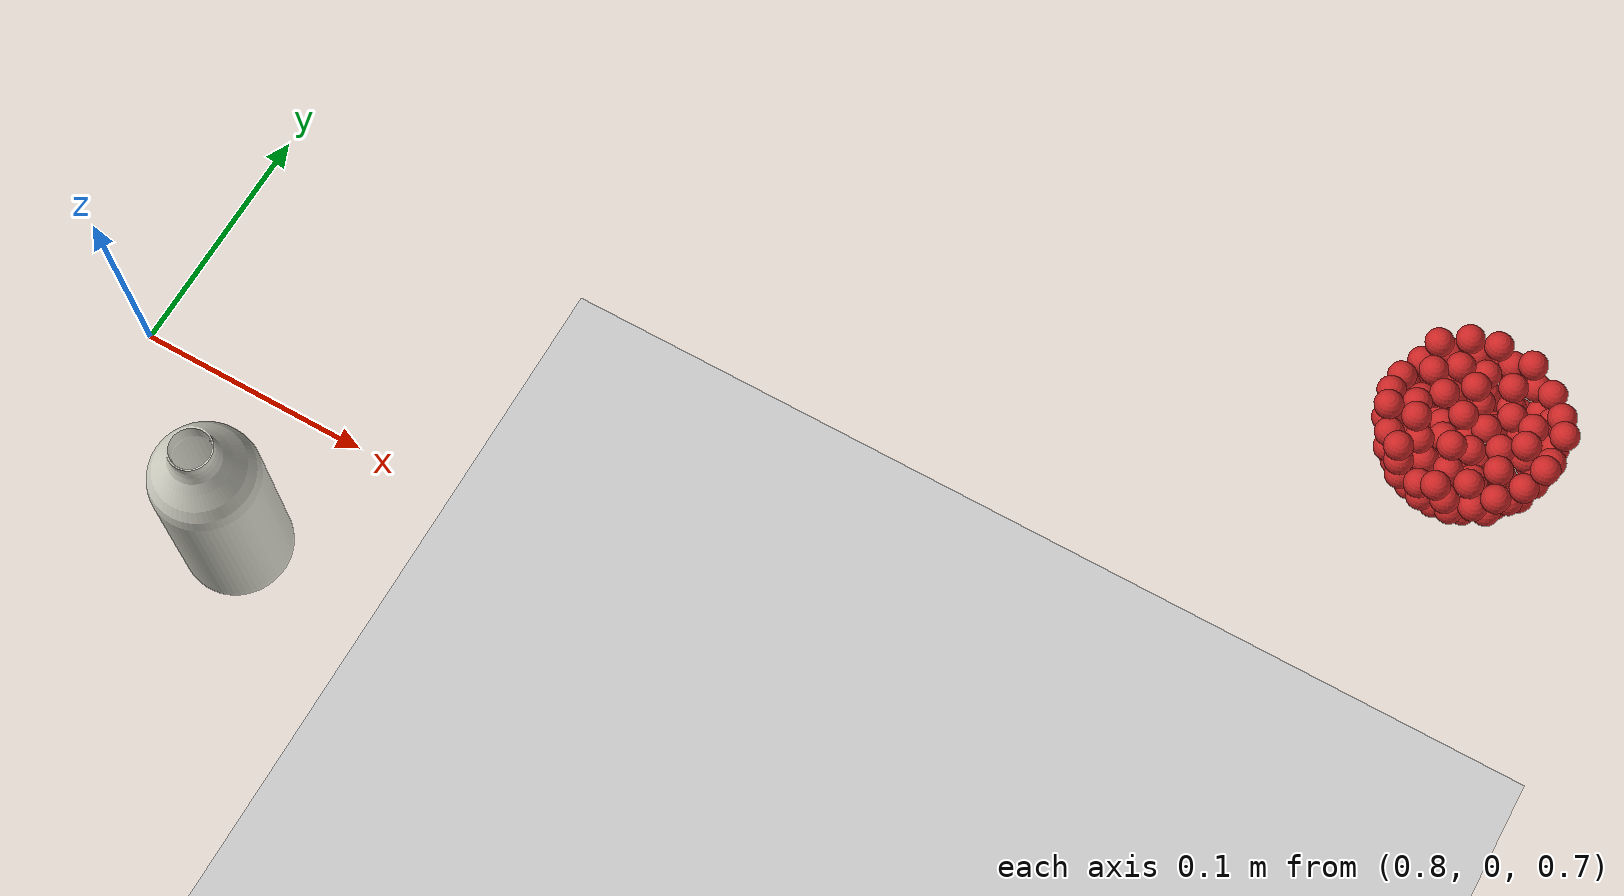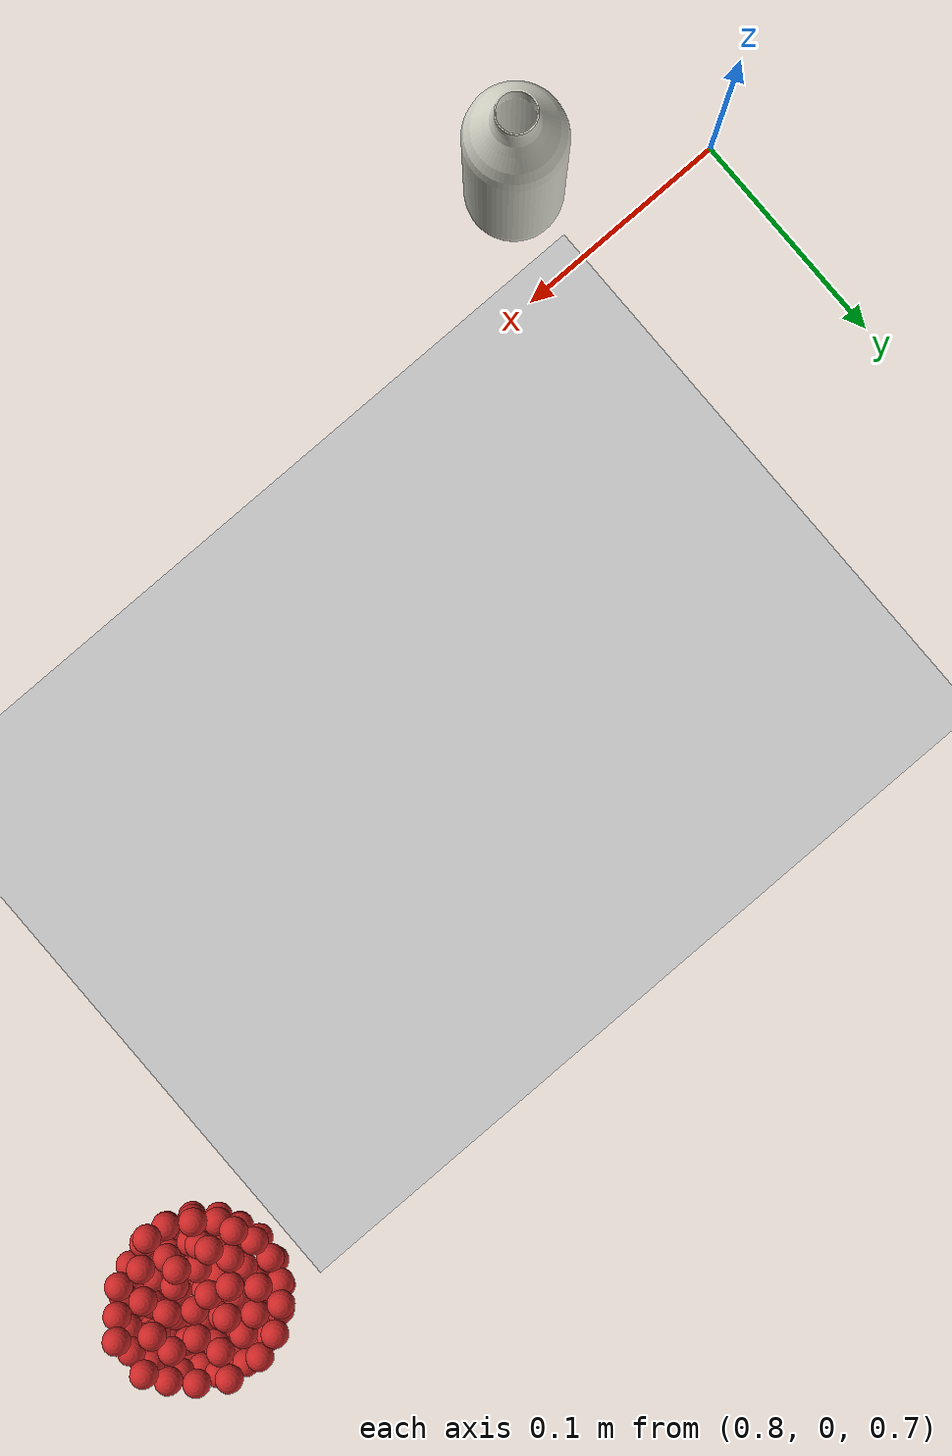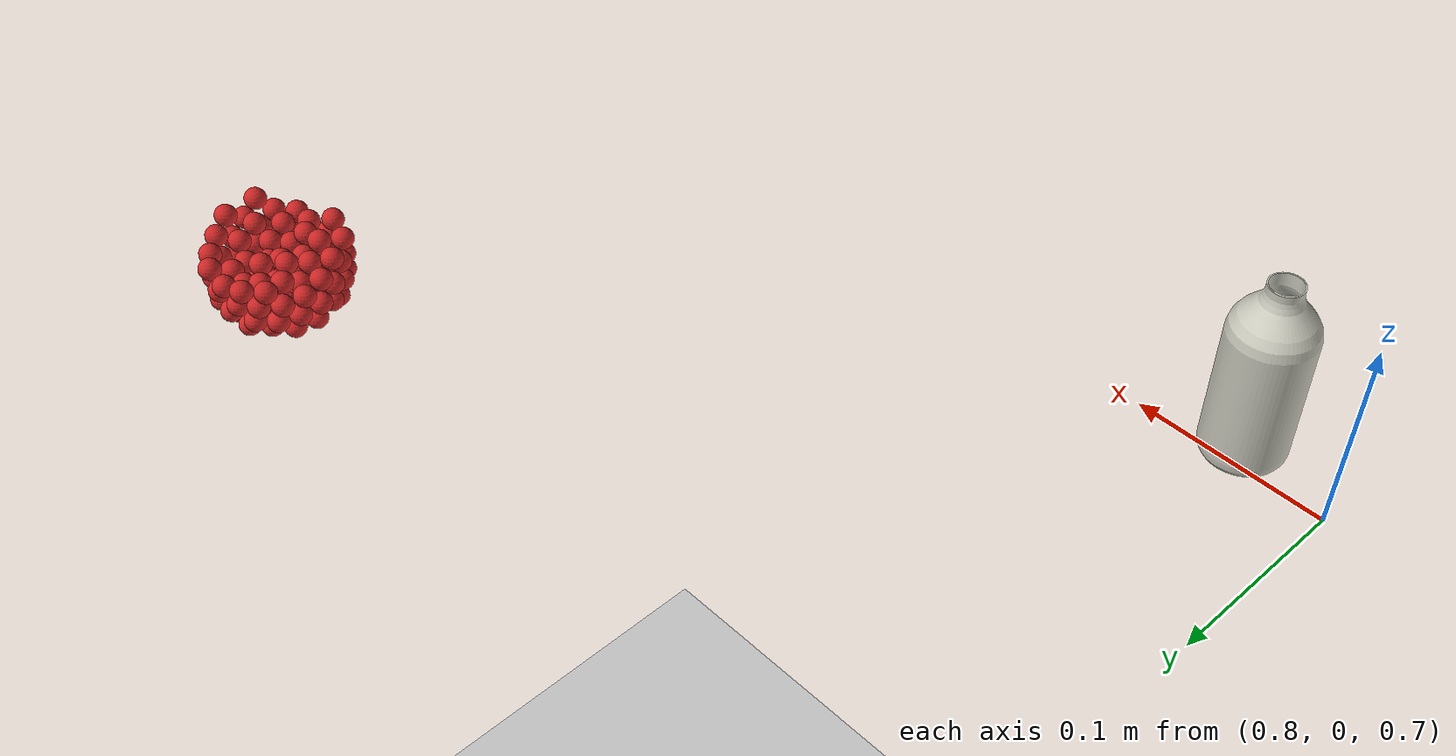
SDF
<sdf version="1.4">
 <world name="default">
  <physics type="ode">
   <gravity>0 0 -9.81</gravity>
   <ode>
    <solver><type>quick</type><iters>20</iters><sor>1</sor></solver>
    <constraints>
     <cfm>0</cfm>
     <erp>0.2</erp>
     <contact_max_correcting_vel>100</contact_max_correcting_vel>
     <contact_surface_layer>0</contact_surface_layer>
    </constraints>
   </ode>
   <real_time_update_rate>1000</real_time_update_rate>
   <max_step_size>0.001</max_step_size>
   <real_time_factor>1</real_time_factor>
  </physics>
  <light name="sun" type="directional">
   <pose>0 0 10 0 -0 0</pose>
   <diffuse>0.8 0.8 0.8 1</diffuse>
   <specular>0.2 0.2 0.2 1</specular>
   <attenuation>
    <range>1000</range>
    <constant>0.9</constant>
    <linear>0.01</linear>
    <quadratic>0.001</quadratic>
   </attenuation>
   <direction>-0.5 0.1 -0.9</direction>
  </light>
  <model name="ground_plane">
   <static>1</static>
   <link name="link">
    <collision name="collision">
     <geometry><plane><normal>0 0 1</normal><size>100 100</size></plane></geometry>
     <surface><friction><ode><mu>100</mu><mu2>50</mu2></ode></friction></surface>
    </collision>
    <visual name="visual">
     <cast_shadows>0</cast_shadows>
     <geometry><plane><normal>0 0 1</normal><size>100 100</size></plane></geometry>
     <material>
      <script><uri>file://media/materials/scripts/gazebo.material</uri><name>Gazebo/Grey</name></script>
     </material>
    </visual>
    <velocity_decay><linear>0</linear><angular>0</angular></velocity_decay>
   </link>
  </model>
  <scene><ambient>0.4 0.4 0.4 1</ambient><background>0.7 0.7 0.7 1</background><shadows>1</shadows></scene>
  <spherical_coordinates>
   <surface_model>EARTH_WGS84</surface_model>
   <latitude_deg>0</latitude_deg>
   <longitude_deg>0</longitude_deg>
   <elevation>0</elevation>
   <heading_deg>0</heading_deg>
  </spherical_coordinates>
  <model name="milk_bottle">
   <static>0</static>
   <link name="link">
    <inertial>
     <mass>0.25</mass>
     <inertia><ixx>0</ixx><ixy>0</ixy><ixz>0</ixz><iyy>0</iyy><iyz>0</iyz><izz>0</izz></inertia>
    </inertial>
    <collision name="colision1">
     <geometry>
      <mesh><uri>model://milk_bottle/meshes/milk_bottle.dae</uri><scale>0.5 0.5 0.5</scale></mesh>
     </geometry>
    </collision>
    <visual name="visual1">
     <geometry>
      <mesh><uri>model://milk_bottle/meshes/milk_bottle.dae</uri><scale>0.5 0.5 0.5</scale></mesh>
     </geometry>
     <material>
      <script><uri>file://media/materials/scripts/gazebo.material</uri><name>Gazebo/PaintedWall</name></script>
     </material>
    </visual>
    <velocity_decay><linear>0</linear><angular>0</angular></velocity_decay>
   </link>
   <pose>0.867059 -0.048695 0.706404 -0.003132 0.001128 -0.000299</pose>
  </model>
  <model name="sphere0">
   <pose>-0.008449 -0.022596 -0.039328 0.014462 -0.011872 0.001814</pose>
   <link name="link">
    <pose>1.27614 0.232149 0.722288 0 -0 0</pose>
    <inertial>
     <mass>0.001</mass>
     <inertia><ixx>0.004</ixx><ixy>0</ixy><ixz>0</ixz><iyy>0.004</iyy><iyz>0</iyz><izz>0.004</izz></inertia>
    </inertial>
    <collision name="collision">
     <surface>
      <contact><ode><kp>1e+10</kp><kd>1</kd></ode></contact>
      <friction><ode><mu>0.01</mu><mu2>0.01</mu2></ode></friction>
     </surface>
     <geometry><sphere><radius>0.006</radius></sphere></geometry>
    </collision>
    <visual name="visual">
     <geometry><sphere><radius>0.006</radius></sphere></geometry>
     <material>
      <script><uri>file://media/materials/scripts/gazebo.material</uri><name>Gazebo/Red</name></script>
     </material>
    </visual>
    <velocity_decay><linear>0</linear><angular>0</angular></velocity_decay>
   </link>
   <static>0</static>
  </model>
  <model name="sphere1">
   <pose>-0.033563 -0.052771 -0.021208 -0.03485 0.01136 -0.002758</pose>
   <link name="link">
    <pose>1.28814 0.232149 0.722288 0 -0 0</pose>
    <inertial>
     <mass>0.001</mass>
     <inertia><ixx>0.004</ixx><ixy>0</ixy><ixz>0</ixz><iyy>0.004</iyy><iyz>0</iyz><izz>0.004</izz></inertia>
    </inertial>
    <collision name="collision">
     <surface>
      <contact><ode><kp>1e+10</kp><kd>1</kd></ode></contact>
      <friction><ode><mu>0.01</mu><mu2>0.01</mu2></ode></friction>
     </surface>
     <geometry><sphere><radius>0.006</radius></sphere></geometry>
    </collision>
    <visual name="visual">
     <geometry><sphere><radius>0.006</radius></sphere></geometry>
     <material>
      <script><uri>file://media/materials/scripts/gazebo.material</uri><name>Gazebo/Red</name></script>
     </material>
    </visual>
    <velocity_decay><linear>0</linear><angular>0</angular></velocity_decay>
   </link>
   <static>0</static>
  </model>
  <model name="sphere2">
   <pose>-0.050173 -0.010075 -0.040103 0.01037 -0.001392 0.001848</pose>
   <link name="link">
    <pose>1.30014 0.232149 0.722288 0 -0 0</pose>
    <inertial>
     <mass>0.001</mass>
     <inertia><ixx>0.004</ixx><ixy>0</ixy><ixz>0</ixz><iyy>0.004</iyy><iyz>0</iyz><izz>0.004</izz></inertia>
    </inertial>
    <collision name="collision">
     <surface>
      <contact><ode><kp>1e+10</kp><kd>1</kd></ode></contact>
      <friction><ode><mu>0.01</mu><mu2>0.01</mu2></ode></friction>
     </surface>
     <geometry><sphere><radius>0.006</radius></sphere></geometry>
    </collision>
    <visual name="visual">
     <geometry><sphere><radius>0.006</radius></sphere></geometry>
     <material>
      <script><uri>file://media/materials/scripts/gazebo.material</uri><name>Gazebo/Red</name></script>
     </material>
    </visual>
    <velocity_decay><linear>0</linear><angular>0</angular></velocity_decay>
   </link>
   <static>0</static>
  </model>
  <model name="sphere3">
   <pose>-0.028546 -0.044237 -0.027117 -0.0037 0.01088 0.004462</pose>
   <link name="link">
    <pose>1.27614 0.244149 0.722288 0 -0 0</pose>
    <inertial>
     <mass>0.001</mass>
     <inertia><ixx>0.004</ixx><ixy>0</ixy><ixz>0</ixz><iyy>0.004</iyy><iyz>0</iyz><izz>0.004</izz></inertia>
    </inertial>
    <collision name="collision">
     <surface>
      <contact><ode><kp>1e+10</kp><kd>1</kd></ode></contact>
      <friction><ode><mu>0.01</mu><mu2>0.01</mu2></ode></friction>
     </surface>
     <geometry><sphere><radius>0.006</radius></sphere></geometry>
    </collision>
    <visual name="visual">
     <geometry><sphere><radius>0.006</radius></sphere></geometry>
     <material>
      <script><uri>file://media/materials/scripts/gazebo.material</uri><name>Gazebo/Red</name></script>
     </material>
    </visual>
    <velocity_decay><linear>0</linear><angular>0</angular></velocity_decay>
   </link>
   <static>0</static>
  </model>
  <model name="sphere4">
   <pose>-0.014802 -0.025122 -0.033295 -0.000353 -0.001627 -0.000772</pose>
   <link name="link">
    <pose>1.28814 0.244149 0.722288 0 -0 0</pose>
    <inertial>
     <mass>0.001</mass>
     <inertia><ixx>0.004</ixx><ixy>0</ixy><ixz>0</ixz><iyy>0.004</iyy><iyz>0</iyz><izz>0.004</izz></inertia>
    </inertial>
    <collision name="collision">
     <surface>
      <contact><ode><kp>1e+10</kp><kd>1</kd></ode></contact>
      <friction><ode><mu>0.01</mu><mu2>0.01</mu2></ode></friction>
     </surface>
     <geometry><sphere><radius>0.006</radius></sphere></geometry>
    </collision>
    <visual name="visual">
     <geometry><sphere><radius>0.006</radius></sphere></geometry>
     <material>
      <script><uri>file://media/materials/scripts/gazebo.material</uri><name>Gazebo/Red</name></script>
     </material>
    </visual>
    <velocity_decay><linear>0</linear><angular>0</angular></velocity_decay>
   </link>
   <static>0</static>
  </model>
  <model name="sphere5">
   <pose>-0.028078 -0.06221 -0.053725 -0.030292 -0.005125 -0.000564</pose>
   <link name="link">
    <pose>1.30014 0.244149 0.722288 0 -0 0</pose>
    <inertial>
     <mass>0.001</mass>
     <inertia><ixx>0.004</ixx><ixy>0</ixy><ixz>0</ixz><iyy>0.004</iyy><iyz>0</iyz><izz>0.004</izz></inertia>
    </inertial>
    <collision name="collision">
     <surface>
      <contact><ode><kp>1e+10</kp><kd>1</kd></ode></contact>
      <friction><ode><mu>0.01</mu><mu2>0.01</mu2></ode></friction>
     </surface>
     <geometry><sphere><radius>0.006</radius></sphere></geometry>
    </collision>
    <visual name="visual">
     <geometry><sphere><radius>0.006</radius></sphere></geometry>
     <material>
      <script><uri>file://media/materials/scripts/gazebo.material</uri><name>Gazebo/Red</name></script>
     </material>
    </visual>
    <velocity_decay><linear>0</linear><angular>0</angular></velocity_decay>
   </link>
   <static>0</static>
  </model>
  <model name="sphere6">
   <pose>-0.032901 -0.03095 -0.022914 -0.000748 0.003173 -0.000882</pose>
   <link name="link">
    <pose>1.27614 0.256149 0.722288 0 -0 0</pose>
    <inertial>
     <mass>0.001</mass>
     <inertia><ixx>0.004</ixx><ixy>0</ixy><ixz>0</ixz><iyy>0.004</iyy><iyz>0</iyz><izz>0.004</izz></inertia>
    </inertial>
    <collision name="collision">
     <surface>
      <contact><ode><kp>1e+10</kp><kd>1</kd></ode></contact>
      <friction><ode><mu>0.01</mu><mu2>0.01</mu2></ode></friction>
     </surface>
     <geometry><sphere><radius>0.006</radius></sphere></geometry>
    </collision>
    <visual name="visual">
     <geometry><sphere><radius>0.006</radius></sphere></geometry>
     <material>
      <script><uri>file://media/materials/scripts/gazebo.material</uri><name>Gazebo/Red</name></script>
     </material>
    </visual>
    <velocity_decay><linear>0</linear><angular>0</angular></velocity_decay>
   </link>
   <static>0</static>
  </model>
  <model name="sphere7">
   <pose>-0.045309 -0.013871 -0.03616 0.003074 0.015054 0.000154</pose>
   <link name="link">
    <pose>1.28814 0.256149 0.722288 0 -0 0</pose>
    <inertial>
     <mass>0.001</mass>
     <inertia><ixx>0.004</ixx><ixy>0</ixy><ixz>0</ixz><iyy>0.004</iyy><iyz>0</iyz><izz>0.004</izz></inertia>
    </inertial>
    <collision name="collision">
     <surface>
      <contact><ode><kp>1e+10</kp><kd>1</kd></ode></contact>
      <friction><ode><mu>0.01</mu><mu2>0.01</mu2></ode></friction>
     </surface>
     <geometry><sphere><radius>0.006</radius></sphere></geometry>
    </collision>
    <visual name="visual">
     <geometry><sphere><radius>0.006</radius></sphere></geometry>
     <material>
      <script><uri>file://media/materials/scripts/gazebo.material</uri><name>Gazebo/Red</name></script>
     </material>
    </visual>
    <velocity_decay><linear>0</linear><angular>0</angular></velocity_decay>
   </link>
   <static>0</static>
  </model>
  <model name="sphere8">
   <pose>-0.018767 -0.053673 -0.057546 0.003739 -0.001351 0.000569</pose>
   <link name="link">
    <pose>1.30014 0.256149 0.722288 0 -0 0</pose>
    <inertial>
     <mass>0.001</mass>
     <inertia><ixx>0.004</ixx><ixy>0</ixy><ixz>0</ixz><iyy>0.004</iyy><iyz>0</iyz><izz>0.004</izz></inertia>
    </inertial>
    <collision name="collision">
     <surface>
      <contact><ode><kp>1e+10</kp><kd>1</kd></ode></contact>
      <friction><ode><mu>0.01</mu><mu2>0.01</mu2></ode></friction>
     </surface>
     <geometry><sphere><radius>0.006</radius></sphere></geometry>
    </collision>
    <visual name="visual">
     <geometry><sphere><radius>0.006</radius></sphere></geometry>
     <material>
      <script><uri>file://media/materials/scripts/gazebo.material</uri><name>Gazebo/Red</name></script>
     </material>
    </visual>
    <velocity_decay><linear>0</linear><angular>0</angular></velocity_decay>
   </link>
   <static>0</static>
  </model>
  <model name="sphere9">
   <pose>-0.015296 -0.01818 -0.030059 0.000717 -0.001454 0.000546</pose>
   <link name="link">
    <pose>1.27614 0.232149 0.734288 0 -0 0</pose>
    <inertial>
     <mass>0.001</mass>
     <inertia><ixx>0.004</ixx><ixy>0</ixy><ixz>0</ixz><iyy>0.004</iyy><iyz>0</iyz><izz>0.004</izz></inertia>
    </inertial>
    <collision name="collision">
     <surface>
      <contact><ode><kp>1e+10</kp><kd>1</kd></ode></contact>
      <friction><ode><mu>0.01</mu><mu2>0.01</mu2></ode></friction>
     </surface>
     <geometry><sphere><radius>0.006</radius></sphere></geometry>
    </collision>
    <visual name="visual">
     <geometry><sphere><radius>0.006</radius></sphere></geometry>
     <material>
      <script><uri>file://media/materials/scripts/gazebo.material</uri><name>Gazebo/Red</name></script>
     </material>
    </visual>
    <velocity_decay><linear>0</linear><angular>0</angular></velocity_decay>
   </link>
   <static>0</static>
  </model>
  <model name="sphere10">
   <pose>-0.044418 -0.017472 -0.045919 -0.00333 0.011076 0.00042</pose>
   <link name="link">
    <pose>1.28814 0.232149 0.734288 0 -0 0</pose>
    <inertial>
     <mass>0.001</mass>
     <inertia><ixx>0.004</ixx><ixy>0</ixy><ixz>0</ixz><iyy>0.004</iyy><iyz>0</iyz><izz>0.004</izz></inertia>
    </inertial>
    <collision name="collision">
     <surface>
      <contact><ode><kp>1e+10</kp><kd>1</kd></ode></contact>
      <friction><ode><mu>0.01</mu><mu2>0.01</mu2></ode></friction>
     </surface>
     <geometry><sphere><radius>0.006</radius></sphere></geometry>
    </collision>
    <visual name="visual">
     <geometry><sphere><radius>0.006</radius></sphere></geometry>
     <material>
      <script><uri>file://media/materials/scripts/gazebo.material</uri><name>Gazebo/Red</name></script>
     </material>
    </visual>
    <velocity_decay><linear>0</linear><angular>0</angular></velocity_decay>
   </link>
   <static>0</static>
  </model>
  <model name="sphere11">
   <pose>-0.052728 -0.062204 -0.032076 -0.055371 0.015929 -0.000204</pose>
   <link name="link">
    <pose>1.30014 0.232149 0.734288 0 -0 0</pose>
    <inertial>
     <mass>0.001</mass>
     <inertia><ixx>0.004</ixx><ixy>0</ixy><ixz>0</ixz><iyy>0.004</iyy><iyz>0</iyz><izz>0.004</izz></inertia>
    </inertial>
    <collision name="collision">
     <surface>
      <contact><ode><kp>1e+10</kp><kd>1</kd></ode></contact>
      <friction><ode><mu>0.01</mu><mu2>0.01</mu2></ode></friction>
     </surface>
     <geometry><sphere><radius>0.006</radius></sphere></geometry>
    </collision>
    <visual name="visual">
     <geometry><sphere><radius>0.006</radius></sphere></geometry>
     <material>
      <script><uri>file://media/materials/scripts/gazebo.material</uri><name>Gazebo/Red</name></script>
     </material>
    </visual>
    <velocity_decay><linear>0</linear><angular>0</angular></velocity_decay>
   </link>
   <static>0</static>
  </model>
  <model name="sphere12">
   <pose>-0.013517 -0.018649 -0.062397 -0.002256 -0.005057 0.000115</pose>
   <link name="link">
    <pose>1.27614 0.244149 0.734288 0 -0 0</pose>
    <inertial>
     <mass>0.001</mass>
     <inertia><ixx>0.004</ixx><ixy>0</ixy><ixz>0</ixz><iyy>0.004</iyy><iyz>0</iyz><izz>0.004</izz></inertia>
    </inertial>
    <collision name="collision">
     <surface>
      <contact><ode><kp>1e+10</kp><kd>1</kd></ode></contact>
      <friction><ode><mu>0.01</mu><mu2>0.01</mu2></ode></friction>
     </surface>
     <geometry><sphere><radius>0.006</radius></sphere></geometry>
    </collision>
    <visual name="visual">
     <geometry><sphere><radius>0.006</radius></sphere></geometry>
     <material>
      <script><uri>file://media/materials/scripts/gazebo.material</uri><name>Gazebo/Red</name></script>
     </material>
    </visual>
    <velocity_decay><linear>0</linear><angular>0</angular></velocity_decay>
   </link>
   <static>0</static>
  </model>
  <model name="sphere13">
   <pose>-0.0034 -0.008162 -0.074705 0.000972 -0.005916 1.1e-05</pose>
   <link name="link">
    <pose>1.28814 0.244149 0.734288 0 -0 0</pose>
    <inertial>
     <mass>0.001</mass>
     <inertia><ixx>0.004</ixx><ixy>0</ixy><ixz>0</ixz><iyy>0.004</iyy><iyz>0</iyz><izz>0.004</izz></inertia>
    </inertial>
    <collision name="collision">
     <surface>
      <contact><ode><kp>1e+10</kp><kd>1</kd></ode></contact>
      <friction><ode><mu>0.01</mu><mu2>0.01</mu2></ode></friction>
     </surface>
     <geometry><sphere><radius>0.006</radius></sphere></geometry>
    </collision>
    <visual name="visual">
     <geometry><sphere><radius>0.006</radius></sphere></geometry>
     <material>
      <script><uri>file://media/materials/scripts/gazebo.material</uri><name>Gazebo/Red</name></script>
     </material>
    </visual>
    <velocity_decay><linear>0</linear><angular>0</angular></velocity_decay>
   </link>
   <static>0</static>
  </model>
  <model name="sphere14">
   <pose>-0.015831 -0.045538 -0.065508 -0.018202 -0.002482 0.000292</pose>
   <link name="link">
    <pose>1.30014 0.244149 0.734288 0 -0 0</pose>
    <inertial>
     <mass>0.001</mass>
     <inertia><ixx>0.004</ixx><ixy>0</ixy><ixz>0</ixz><iyy>0.004</iyy><iyz>0</iyz><izz>0.004</izz></inertia>
    </inertial>
    <collision name="collision">
     <surface>
      <contact><ode><kp>1e+10</kp><kd>1</kd></ode></contact>
      <friction><ode><mu>0.01</mu><mu2>0.01</mu2></ode></friction>
     </surface>
     <geometry><sphere><radius>0.006</radius></sphere></geometry>
    </collision>
    <visual name="visual">
     <geometry><sphere><radius>0.006</radius></sphere></geometry>
     <material>
      <script><uri>file://media/materials/scripts/gazebo.material</uri><name>Gazebo/Red</name></script>
     </material>
    </visual>
    <velocity_decay><linear>0</linear><angular>0</angular></velocity_decay>
   </link>
   <static>0</static>
  </model>
  <model name="sphere15">
   <pose>-0.003786 -0.027529 -0.077509 0.020082 -0.032112 0.001138</pose>
   <link name="link">
    <pose>1.27614 0.256149 0.734288 0 -0 0</pose>
    <inertial>
     <mass>0.001</mass>
     <inertia><ixx>0.004</ixx><ixy>0</ixy><ixz>0</ixz><iyy>0.004</iyy><iyz>0</iyz><izz>0.004</izz></inertia>
    </inertial>
    <collision name="collision">
     <surface>
      <contact><ode><kp>1e+10</kp><kd>1</kd></ode></contact>
      <friction><ode><mu>0.01</mu><mu2>0.01</mu2></ode></friction>
     </surface>
     <geometry><sphere><radius>0.006</radius></sphere></geometry>
    </collision>
    <visual name="visual">
     <geometry><sphere><radius>0.006</radius></sphere></geometry>
     <material>
      <script><uri>file://media/materials/scripts/gazebo.material</uri><name>Gazebo/Red</name></script>
     </material>
    </visual>
    <velocity_decay><linear>0</linear><angular>0</angular></velocity_decay>
   </link>
   <static>0</static>
  </model>
  <model name="sphere16">
   <pose>-0.032975 0.000135 -0.056876 0.010404 0.009764 -0.000229</pose>
   <link name="link">
    <pose>1.28814 0.256149 0.734288 0 -0 0</pose>
    <inertial>
     <mass>0.001</mass>
     <inertia><ixx>0.004</ixx><ixy>0</ixy><ixz>0</ixz><iyy>0.004</iyy><iyz>0</iyz><izz>0.004</izz></inertia>
    </inertial>
    <collision name="collision">
     <surface>
      <contact><ode><kp>1e+10</kp><kd>1</kd></ode></contact>
      <friction><ode><mu>0.01</mu><mu2>0.01</mu2></ode></friction>
     </surface>
     <geometry><sphere><radius>0.006</radius></sphere></geometry>
    </collision>
    <visual name="visual">
     <geometry><sphere><radius>0.006</radius></sphere></geometry>
     <material>
      <script><uri>file://media/materials/scripts/gazebo.material</uri><name>Gazebo/Red</name></script>
     </material>
    </visual>
    <velocity_decay><linear>0</linear><angular>0</angular></velocity_decay>
   </link>
   <static>0</static>
  </model>
  <model name="sphere17">
   <pose>-0.033035 0.015816 -0.044256 0.023969 0.021809 0.000223</pose>
   <link name="link">
    <pose>1.30014 0.256149 0.734288 0 -0 0</pose>
    <inertial>
     <mass>0.001</mass>
     <inertia><ixx>0.004</ixx><ixy>0</ixy><ixz>0</ixz><iyy>0.004</iyy><iyz>0</iyz><izz>0.004</izz></inertia>
    </inertial>
    <collision name="collision">
     <surface>
      <contact><ode><kp>1e+10</kp><kd>1</kd></ode></contact>
      <friction><ode><mu>0.01</mu><mu2>0.01</mu2></ode></friction>
     </surface>
     <geometry><sphere><radius>0.006</radius></sphere></geometry>
    </collision>
    <visual name="visual">
     <geometry><sphere><radius>0.006</radius></sphere></geometry>
     <material>
      <script><uri>file://media/materials/scripts/gazebo.material</uri><name>Gazebo/Red</name></script>
     </material>
    </visual>
    <velocity_decay><linear>0</linear><angular>0</angular></velocity_decay>
   </link>
   <static>0</static>
  </model>
  <model name="sphere18">
   <pose>-0.03367 -0.007862 -0.06187 -0.005235 0.01192 0.000236</pose>
   <link name="link">
    <pose>1.27614 0.232149 0.746288 0 -0 0</pose>
    <inertial>
     <mass>0.001</mass>
     <inertia><ixx>0.004</ixx><ixy>0</ixy><ixz>0</ixz><iyy>0.004</iyy><iyz>0</iyz><izz>0.004</izz></inertia>
    </inertial>
    <collision name="collision">
     <surface>
      <contact><ode><kp>1e+10</kp><kd>1</kd></ode></contact>
      <friction><ode><mu>0.01</mu><mu2>0.01</mu2></ode></friction>
     </surface>
     <geometry><sphere><radius>0.006</radius></sphere></geometry>
    </collision>
    <visual name="visual">
     <geometry><sphere><radius>0.006</radius></sphere></geometry>
     <material>
      <script><uri>file://media/materials/scripts/gazebo.material</uri><name>Gazebo/Red</name></script>
     </material>
    </visual>
    <velocity_decay><linear>0</linear><angular>0</angular></velocity_decay>
   </link>
   <static>0</static>
  </model>
  <model name="sphere19">
   <pose>-0.009811 -0.037376 -0.047543 -0.001053 -0.000103 -0.000936</pose>
   <link name="link">
    <pose>1.28814 0.232149 0.746288 0 -0 0</pose>
    <inertial>
     <mass>0.001</mass>
     <inertia><ixx>0.004</ixx><ixy>0</ixy><ixz>0</ixz><iyy>0.004</iyy><iyz>0</iyz><izz>0.004</izz></inertia>
    </inertial>
    <collision name="collision">
     <surface>
      <contact><ode><kp>1e+10</kp><kd>1</kd></ode></contact>
      <friction><ode><mu>0.01</mu><mu2>0.01</mu2></ode></friction>
     </surface>
     <geometry><sphere><radius>0.006</radius></sphere></geometry>
    </collision>
    <visual name="visual">
     <geometry><sphere><radius>0.006</radius></sphere></geometry>
     <material>
      <script><uri>file://media/materials/scripts/gazebo.material</uri><name>Gazebo/Red</name></script>
     </material>
    </visual>
    <velocity_decay><linear>0</linear><angular>0</angular></velocity_decay>
   </link>
   <static>0</static>
  </model>
  <model name="sphere20">
   <pose>-0.025354 -0.026452 -0.072197 0.012664 -0.000145 0.000498</pose>
   <link name="link">
    <pose>1.30014 0.232149 0.746288 0 -0 0</pose>
    <inertial>
     <mass>0.001</mass>
     <inertia><ixx>0.004</ixx><ixy>0</ixy><ixz>0</ixz><iyy>0.004</iyy><iyz>0</iyz><izz>0.004</izz></inertia>
    </inertial>
    <collision name="collision">
     <surface>
      <contact><ode><kp>1e+10</kp><kd>1</kd></ode></contact>
      <friction><ode><mu>0.01</mu><mu2>0.01</mu2></ode></friction>
     </surface>
     <geometry><sphere><radius>0.006</radius></sphere></geometry>
    </collision>
    <visual name="visual">
     <geometry><sphere><radius>0.006</radius></sphere></geometry>
     <material>
      <script><uri>file://media/materials/scripts/gazebo.material</uri><name>Gazebo/Red</name></script>
     </material>
    </visual>
    <velocity_decay><linear>0</linear><angular>0</angular></velocity_decay>
   </link>
   <static>0</static>
  </model>
  <model name="sphere21">
   <pose>-0.023843 -0.036713 -0.051757 -0.00138 0.000324 -2.7e-05</pose>
   <link name="link">
    <pose>1.27614 0.244149 0.746288 0 -0 0</pose>
    <inertial>
     <mass>0.001</mass>
     <inertia><ixx>0.004</ixx><ixy>0</ixy><ixz>0</ixz><iyy>0.004</iyy><iyz>0</iyz><izz>0.004</izz></inertia>
    </inertial>
    <collision name="collision">
     <surface>
      <contact><ode><kp>1e+10</kp><kd>1</kd></ode></contact>
      <friction><ode><mu>0.01</mu><mu2>0.01</mu2></ode></friction>
     </surface>
     <geometry><sphere><radius>0.006</radius></sphere></geometry>
    </collision>
    <visual name="visual">
     <geometry><sphere><radius>0.006</radius></sphere></geometry>
     <material>
      <script><uri>file://media/materials/scripts/gazebo.material</uri><name>Gazebo/Red</name></script>
     </material>
    </visual>
    <velocity_decay><linear>0</linear><angular>0</angular></velocity_decay>
   </link>
   <static>0</static>
  </model>
  <model name="sphere22">
   <pose>-0.027319 -0.016902 -0.080034 0.006578 0.000397 -0.00035</pose>
   <link name="link">
    <pose>1.28814 0.244149 0.746288 0 -0 0</pose>
    <inertial>
     <mass>0.001</mass>
     <inertia><ixx>0.004</ixx><ixy>0</ixy><ixz>0</ixz><iyy>0.004</iyy><iyz>0</iyz><izz>0.004</izz></inertia>
    </inertial>
    <collision name="collision">
     <surface>
      <contact><ode><kp>1e+10</kp><kd>1</kd></ode></contact>
      <friction><ode><mu>0.01</mu><mu2>0.01</mu2></ode></friction>
     </surface>
     <geometry><sphere><radius>0.006</radius></sphere></geometry>
    </collision>
    <visual name="visual">
     <geometry><sphere><radius>0.006</radius></sphere></geometry>
     <material>
      <script><uri>file://media/materials/scripts/gazebo.material</uri><name>Gazebo/Red</name></script>
     </material>
    </visual>
    <velocity_decay><linear>0</linear><angular>0</angular></velocity_decay>
   </link>
   <static>0</static>
  </model>
  <model name="sphere23">
   <pose>-0.029251 -0.025642 -0.080473 0.00396 -0.000479 -0.000592</pose>
   <link name="link">
    <pose>1.30014 0.244149 0.746288 0 -0 0</pose>
    <inertial>
     <mass>0.001</mass>
     <inertia><ixx>0.004</ixx><ixy>0</ixy><ixz>0</ixz><iyy>0.004</iyy><iyz>0</iyz><izz>0.004</izz></inertia>
    </inertial>
    <collision name="collision">
     <surface>
      <contact><ode><kp>1e+10</kp><kd>1</kd></ode></contact>
      <friction><ode><mu>0.01</mu><mu2>0.01</mu2></ode></friction>
     </surface>
     <geometry><sphere><radius>0.006</radius></sphere></geometry>
    </collision>
    <visual name="visual">
     <geometry><sphere><radius>0.006</radius></sphere></geometry>
     <material>
      <script><uri>file://media/materials/scripts/gazebo.material</uri><name>Gazebo/Red</name></script>
     </material>
    </visual>
    <velocity_decay><linear>0</linear><angular>0</angular></velocity_decay>
   </link>
   <static>0</static>
  </model>
  <model name="sphere24">
   <pose>0.023964 -0.015748 -0.15087 0.007295 -0.064638 0.002877</pose>
   <link name="link">
    <pose>1.27614 0.256149 0.746288 0 -0 0</pose>
    <inertial>
     <mass>0.001</mass>
     <inertia><ixx>0.004</ixx><ixy>0</ixy><ixz>0</ixz><iyy>0.004</iyy><iyz>0</iyz><izz>0.004</izz></inertia>
    </inertial>
    <collision name="collision">
     <surface>
      <contact><ode><kp>1e+10</kp><kd>1</kd></ode></contact>
      <friction><ode><mu>0.01</mu><mu2>0.01</mu2></ode></friction>
     </surface>
     <geometry><sphere><radius>0.006</radius></sphere></geometry>
    </collision>
    <visual name="visual">
     <geometry><sphere><radius>0.006</radius></sphere></geometry>
     <material>
      <script><uri>file://media/materials/scripts/gazebo.material</uri><name>Gazebo/Red</name></script>
     </material>
    </visual>
    <velocity_decay><linear>0</linear><angular>0</angular></velocity_decay>
   </link>
   <static>0</static>
  </model>
  <model name="sphere25">
   <pose>-0.036337 -0.00955 -0.061237 0.000253 -0.001555 -0.000263</pose>
   <link name="link">
    <pose>1.28814 0.256149 0.746288 0 -0 0</pose>
    <inertial>
     <mass>0.001</mass>
     <inertia><ixx>0.004</ixx><ixy>0</ixy><ixz>0</ixz><iyy>0.004</iyy><iyz>0</iyz><izz>0.004</izz></inertia>
    </inertial>
    <collision name="collision">
     <surface>
      <contact><ode><kp>1e+10</kp><kd>1</kd></ode></contact>
      <friction><ode><mu>0.01</mu><mu2>0.01</mu2></ode></friction>
     </surface>
     <geometry><sphere><radius>0.006</radius></sphere></geometry>
    </collision>
    <visual name="visual">
     <geometry><sphere><radius>0.006</radius></sphere></geometry>
     <material>
      <script><uri>file://media/materials/scripts/gazebo.material</uri><name>Gazebo/Red</name></script>
     </material>
    </visual>
    <velocity_decay><linear>0</linear><angular>0</angular></velocity_decay>
   </link>
   <static>0</static>
  </model>
  <model name="sphere26">
   <pose>-0.028305 -0.030061 -0.078205 -0.001105 0.000296 -0.000266</pose>
   <link name="link">
    <pose>1.30014 0.256149 0.746288 0 -0 0</pose>
    <inertial>
     <mass>0.001</mass>
     <inertia><ixx>0.004</ixx><ixy>0</ixy><ixz>0</ixz><iyy>0.004</iyy><iyz>0</iyz><izz>0.004</izz></inertia>
    </inertial>
    <collision name="collision">
     <surface>
      <contact><ode><kp>1e+10</kp><kd>1</kd></ode></contact>
      <friction><ode><mu>0.01</mu><mu2>0.01</mu2></ode></friction>
     </surface>
     <geometry><sphere><radius>0.006</radius></sphere></geometry>
    </collision>
    <visual name="visual">
     <geometry><sphere><radius>0.006</radius></sphere></geometry>
     <material>
      <script><uri>file://media/materials/scripts/gazebo.material</uri><name>Gazebo/Red</name></script>
     </material>
    </visual>
    <velocity_decay><linear>0</linear><angular>0</angular></velocity_decay>
   </link>
   <static>0</static>
  </model>
  <model name="sphere27">
   <pose>-0.015477 -0.031403 -0.068217 0.000595 0.000457 0.000546</pose>
   <link name="link">
    <pose>1.27614 0.232149 0.758288 0 -0 0</pose>
    <inertial>
     <mass>0.001</mass>
     <inertia><ixx>0.004</ixx><ixy>0</ixy><ixz>0</ixz><iyy>0.004</iyy><iyz>0</iyz><izz>0.004</izz></inertia>
    </inertial>
    <collision name="collision">
     <surface>
      <contact><ode><kp>1e+10</kp><kd>1</kd></ode></contact>
      <friction><ode><mu>0.01</mu><mu2>0.01</mu2></ode></friction>
     </surface>
     <geometry><sphere><radius>0.006</radius></sphere></geometry>
    </collision>
    <visual name="visual">
     <geometry><sphere><radius>0.006</radius></sphere></geometry>
     <material>
      <script><uri>file://media/materials/scripts/gazebo.material</uri><name>Gazebo/Red</name></script>
     </material>
    </visual>
    <velocity_decay><linear>0</linear><angular>0</angular></velocity_decay>
   </link>
   <static>0</static>
  </model>
  <model name="sphere28">
   <pose>-0.003416 -0.037625 -0.071615 -0.000766 -0.001145 0.00032</pose>
   <link name="link">
    <pose>1.28814 0.232149 0.758288 0 -0 0</pose>
    <inertial>
     <mass>0.001</mass>
     <inertia><ixx>0.004</ixx><ixy>0</ixy><ixz>0</ixz><iyy>0.004</iyy><iyz>0</iyz><izz>0.004</izz></inertia>
    </inertial>
    <collision name="collision">
     <surface>
      <contact><ode><kp>1e+10</kp><kd>1</kd></ode></contact>
      <friction><ode><mu>0.01</mu><mu2>0.01</mu2></ode></friction>
     </surface>
     <geometry><sphere><radius>0.006</radius></sphere></geometry>
    </collision>
    <visual name="visual">
     <geometry><sphere><radius>0.006</radius></sphere></geometry>
     <material>
      <script><uri>file://media/materials/scripts/gazebo.material</uri><name>Gazebo/Red</name></script>
     </material>
    </visual>
    <velocity_decay><linear>0</linear><angular>0</angular></velocity_decay>
   </link>
   <static>0</static>
  </model>
  <model name="sphere29">
   <pose>-0.024555 -0.015755 -0.081648 0.027044 -0.004769 0.000312</pose>
   <link name="link">
    <pose>1.30014 0.232149 0.758288 0 -0 0</pose>
    <inertial>
     <mass>0.001</mass>
     <inertia><ixx>0.004</ixx><ixy>0</ixy><ixz>0</ixz><iyy>0.004</iyy><iyz>0</iyz><izz>0.004</izz></inertia>
    </inertial>
    <collision name="collision">
     <surface>
      <contact><ode><kp>1e+10</kp><kd>1</kd></ode></contact>
      <friction><ode><mu>0.01</mu><mu2>0.01</mu2></ode></friction>
     </surface>
     <geometry><sphere><radius>0.006</radius></sphere></geometry>
    </collision>
    <visual name="visual">
     <geometry><sphere><radius>0.006</radius></sphere></geometry>
     <material>
      <script><uri>file://media/materials/scripts/gazebo.material</uri><name>Gazebo/Red</name></script>
     </material>
    </visual>
    <velocity_decay><linear>0</linear><angular>0</angular></velocity_decay>
   </link>
   <static>0</static>
  </model>
  <model name="sphere30">
   <pose>-0.009021 -0.004718 -0.069597 0.000796 0.000534 -0.000799</pose>
   <link name="link">
    <pose>1.27614 0.244149 0.758288 0 -0 0</pose>
    <inertial>
     <mass>0.001</mass>
     <inertia><ixx>0.004</ixx><ixy>0</ixy><ixz>0</ixz><iyy>0.004</iyy><iyz>0</iyz><izz>0.004</izz></inertia>
    </inertial>
    <collision name="collision">
     <surface>
      <contact><ode><kp>1e+10</kp><kd>1</kd></ode></contact>
      <friction><ode><mu>0.01</mu><mu2>0.01</mu2></ode></friction>
     </surface>
     <geometry><sphere><radius>0.006</radius></sphere></geometry>
    </collision>
    <visual name="visual">
     <geometry><sphere><radius>0.006</radius></sphere></geometry>
     <material>
      <script><uri>file://media/materials/scripts/gazebo.material</uri><name>Gazebo/Red</name></script>
     </material>
    </visual>
    <velocity_decay><linear>0</linear><angular>0</angular></velocity_decay>
   </link>
   <static>0</static>
  </model>
  <model name="sphere31">
   <pose>-0.027336 -0.022046 -0.072235 0.003035 -0.00092 -0.000655</pose>
   <link name="link">
    <pose>1.28814 0.244149 0.758288 0 -0 0</pose>
    <inertial>
     <mass>0.001</mass>
     <inertia><ixx>0.004</ixx><ixy>0</ixy><ixz>0</ixz><iyy>0.004</iyy><iyz>0</iyz><izz>0.004</izz></inertia>
    </inertial>
    <collision name="collision">
     <surface>
      <contact><ode><kp>1e+10</kp><kd>1</kd></ode></contact>
      <friction><ode><mu>0.01</mu><mu2>0.01</mu2></ode></friction>
     </surface>
     <geometry><sphere><radius>0.006</radius></sphere></geometry>
    </collision>
    <visual name="visual">
     <geometry><sphere><radius>0.006</radius></sphere></geometry>
     <material>
      <script><uri>file://media/materials/scripts/gazebo.material</uri><name>Gazebo/Red</name></script>
     </material>
    </visual>
    <velocity_decay><linear>0</linear><angular>0</angular></velocity_decay>
   </link>
   <static>0</static>
  </model>
  <model name="sphere32">
   <pose>0.00385 -0.01906 -0.075333 0.001472 0.005182 -0.006747</pose>
   <link name="link">
    <pose>1.30014 0.244149 0.758288 0 -0 0</pose>
    <inertial>
     <mass>0.001</mass>
     <inertia><ixx>0.004</ixx><ixy>0</ixy><ixz>0</ixz><iyy>0.004</iyy><iyz>0</iyz><izz>0.004</izz></inertia>
    </inertial>
    <collision name="collision">
     <surface>
      <contact><ode><kp>1e+10</kp><kd>1</kd></ode></contact>
      <friction><ode><mu>0.01</mu><mu2>0.01</mu2></ode></friction>
     </surface>
     <geometry><sphere><radius>0.006</radius></sphere></geometry>
    </collision>
    <visual name="visual">
     <geometry><sphere><radius>0.006</radius></sphere></geometry>
     <material>
      <script><uri>file://media/materials/scripts/gazebo.material</uri><name>Gazebo/Red</name></script>
     </material>
    </visual>
    <velocity_decay><linear>0</linear><angular>0</angular></velocity_decay>
   </link>
   <static>0</static>
  </model>
  <model name="sphere33">
   <pose>0.016946 -0.005899 -0.129261 -0.011122 -0.039329 -0.001441</pose>
   <link name="link">
    <pose>1.27614 0.256149 0.758288 0 -0 0</pose>
    <inertial>
     <mass>0.001</mass>
     <inertia><ixx>0.004</ixx><ixy>0</ixy><ixz>0</ixz><iyy>0.004</iyy><iyz>0</iyz><izz>0.004</izz></inertia>
    </inertial>
    <collision name="collision">
     <surface>
      <contact><ode><kp>1e+10</kp><kd>1</kd></ode></contact>
      <friction><ode><mu>0.01</mu><mu2>0.01</mu2></ode></friction>
     </surface>
     <geometry><sphere><radius>0.006</radius></sphere></geometry>
    </collision>
    <visual name="visual">
     <geometry><sphere><radius>0.006</radius></sphere></geometry>
     <material>
      <script><uri>file://media/materials/scripts/gazebo.material</uri><name>Gazebo/Red</name></script>
     </material>
    </visual>
    <velocity_decay><linear>0</linear><angular>0</angular></velocity_decay>
   </link>
   <static>0</static>
  </model>
  <model name="sphere34">
   <pose>-0.038778 0.007409 -0.055137 0.009541 0.029321 0.000222</pose>
   <link name="link">
    <pose>1.28814 0.256149 0.758288 0 -0 0</pose>
    <inertial>
     <mass>0.001</mass>
     <inertia><ixx>0.004</ixx><ixy>0</ixy><ixz>0</ixz><iyy>0.004</iyy><iyz>0</iyz><izz>0.004</izz></inertia>
    </inertial>
    <collision name="collision">
     <surface>
      <contact><ode><kp>1e+10</kp><kd>1</kd></ode></contact>
      <friction><ode><mu>0.01</mu><mu2>0.01</mu2></ode></friction>
     </surface>
     <geometry><sphere><radius>0.006</radius></sphere></geometry>
    </collision>
    <visual name="visual">
     <geometry><sphere><radius>0.006</radius></sphere></geometry>
     <material>
      <script><uri>file://media/materials/scripts/gazebo.material</uri><name>Gazebo/Red</name></script>
     </material>
    </visual>
    <velocity_decay><linear>0</linear><angular>0</angular></velocity_decay>
   </link>
   <static>0</static>
  </model>
  <model name="sphere35">
   <pose>-0.019421 -0.039285 -0.082713 -0.007987 0.004656 0.000726</pose>
   <link name="link">
    <pose>1.30014 0.256149 0.758288 0 -0 0</pose>
    <inertial>
     <mass>0.001</mass>
     <inertia><ixx>0.004</ixx><ixy>0</ixy><ixz>0</ixz><iyy>0.004</iyy><iyz>0</iyz><izz>0.004</izz></inertia>
    </inertial>
    <collision name="collision">
     <surface>
      <contact><ode><kp>1e+10</kp><kd>1</kd></ode></contact>
      <friction><ode><mu>0.01</mu><mu2>0.01</mu2></ode></friction>
     </surface>
     <geometry><sphere><radius>0.006</radius></sphere></geometry>
    </collision>
    <visual name="visual">
     <geometry><sphere><radius>0.006</radius></sphere></geometry>
     <material>
      <script><uri>file://media/materials/scripts/gazebo.material</uri><name>Gazebo/Red</name></script>
     </material>
    </visual>
    <velocity_decay><linear>0</linear><angular>0</angular></velocity_decay>
   </link>
   <static>0</static>
  </model>
  <model name="sphere36">
   <pose>0.001546 -0.020254 -0.071173 -0.000125 -0.000919 0.000194</pose>
   <link name="link">
    <pose>1.27614 0.232149 0.770288 0 -0 0</pose>
    <inertial>
     <mass>0.001</mass>
     <inertia><ixx>0.004</ixx><ixy>0</ixy><ixz>0</ixz><iyy>0.004</iyy><iyz>0</iyz><izz>0.004</izz></inertia>
    </inertial>
    <collision name="collision">
     <surface>
      <contact><ode><kp>1e+10</kp><kd>1</kd></ode></contact>
      <friction><ode><mu>0.01</mu><mu2>0.01</mu2></ode></friction>
     </surface>
     <geometry><sphere><radius>0.006</radius></sphere></geometry>
    </collision>
    <visual name="visual">
     <geometry><sphere><radius>0.006</radius></sphere></geometry>
     <material>
      <script><uri>file://media/materials/scripts/gazebo.material</uri><name>Gazebo/Red</name></script>
     </material>
    </visual>
    <velocity_decay><linear>0</linear><angular>0</angular></velocity_decay>
   </link>
   <static>0</static>
  </model>
  <model name="sphere37">
   <pose>-0.020075 -0.015986 -0.101192 0.003858 -0.005467 0.001609</pose>
   <link name="link">
    <pose>1.28814 0.232149 0.770288 0 -0 0</pose>
    <inertial>
     <mass>0.001</mass>
     <inertia><ixx>0.004</ixx><ixy>0</ixy><ixz>0</ixz><iyy>0.004</iyy><iyz>0</iyz><izz>0.004</izz></inertia>
    </inertial>
    <collision name="collision">
     <surface>
      <contact><ode><kp>1e+10</kp><kd>1</kd></ode></contact>
      <friction><ode><mu>0.01</mu><mu2>0.01</mu2></ode></friction>
     </surface>
     <geometry><sphere><radius>0.006</radius></sphere></geometry>
    </collision>
    <visual name="visual">
     <geometry><sphere><radius>0.006</radius></sphere></geometry>
     <material>
      <script><uri>file://media/materials/scripts/gazebo.material</uri><name>Gazebo/Red</name></script>
     </material>
    </visual>
    <velocity_decay><linear>0</linear><angular>0</angular></velocity_decay>
   </link>
   <static>0</static>
  </model>
  <model name="sphere38">
   <pose>0.008312 -0.02494 -0.088484 -0.000462 -0.00288 0.000366</pose>
   <link name="link">
    <pose>1.30014 0.232149 0.770288 0 -0 0</pose>
    <inertial>
     <mass>0.001</mass>
     <inertia><ixx>0.004</ixx><ixy>0</ixy><ixz>0</ixz><iyy>0.004</iyy><iyz>0</iyz><izz>0.004</izz></inertia>
    </inertial>
    <collision name="collision">
     <surface>
      <contact><ode><kp>1e+10</kp><kd>1</kd></ode></contact>
      <friction><ode><mu>0.01</mu><mu2>0.01</mu2></ode></friction>
     </surface>
     <geometry><sphere><radius>0.006</radius></sphere></geometry>
    </collision>
    <visual name="visual">
     <geometry><sphere><radius>0.006</radius></sphere></geometry>
     <material>
      <script><uri>file://media/materials/scripts/gazebo.material</uri><name>Gazebo/Red</name></script>
     </material>
    </visual>
    <velocity_decay><linear>0</linear><angular>0</angular></velocity_decay>
   </link>
   <static>0</static>
  </model>
  <model name="sphere39">
   <pose>-0.031011 -0.015107 -0.088257 -0.001722 0.001549 -0.002915</pose>
   <link name="link">
    <pose>1.27614 0.244149 0.770288 0 -0 0</pose>
    <inertial>
     <mass>0.001</mass>
     <inertia><ixx>0.004</ixx><ixy>0</ixy><ixz>0</ixz><iyy>0.004</iyy><iyz>0</iyz><izz>0.004</izz></inertia>
    </inertial>
    <collision name="collision">
     <surface>
      <contact><ode><kp>1e+10</kp><kd>1</kd></ode></contact>
      <friction><ode><mu>0.01</mu><mu2>0.01</mu2></ode></friction>
     </surface>
     <geometry><sphere><radius>0.006</radius></sphere></geometry>
    </collision>
    <visual name="visual">
     <geometry><sphere><radius>0.006</radius></sphere></geometry>
     <material>
      <script><uri>file://media/materials/scripts/gazebo.material</uri><name>Gazebo/Red</name></script>
     </material>
    </visual>
    <velocity_decay><linear>0</linear><angular>0</angular></velocity_decay>
   </link>
   <static>0</static>
  </model>
  <model name="sphere40">
   <pose>-0.026836 -0.014503 -0.087059 -0.000768 -0.004772 0.000233</pose>
   <link name="link">
    <pose>1.28814 0.244149 0.770288 0 -0 0</pose>
    <inertial>
     <mass>0.001</mass>
     <inertia><ixx>0.004</ixx><ixy>0</ixy><ixz>0</ixz><iyy>0.004</iyy><iyz>0</iyz><izz>0.004</izz></inertia>
    </inertial>
    <collision name="collision">
     <surface>
      <contact><ode><kp>1e+10</kp><kd>1</kd></ode></contact>
      <friction><ode><mu>0.01</mu><mu2>0.01</mu2></ode></friction>
     </surface>
     <geometry><sphere><radius>0.006</radius></sphere></geometry>
    </collision>
    <visual name="visual">
     <geometry><sphere><radius>0.006</radius></sphere></geometry>
     <material>
      <script><uri>file://media/materials/scripts/gazebo.material</uri><name>Gazebo/Red</name></script>
     </material>
    </visual>
    <velocity_decay><linear>0</linear><angular>0</angular></velocity_decay>
   </link>
   <static>0</static>
  </model>
  <model name="sphere41">
   <pose>-0.008737 -0.033744 -0.087392 -0.000104 -0.001694 -0.000369</pose>
   <link name="link">
    <pose>1.30014 0.244149 0.770288 0 -0 0</pose>
    <inertial>
     <mass>0.001</mass>
     <inertia><ixx>0.004</ixx><ixy>0</ixy><ixz>0</ixz><iyy>0.004</iyy><iyz>0</iyz><izz>0.004</izz></inertia>
    </inertial>
    <collision name="collision">
     <surface>
      <contact><ode><kp>1e+10</kp><kd>1</kd></ode></contact>
      <friction><ode><mu>0.01</mu><mu2>0.01</mu2></ode></friction>
     </surface>
     <geometry><sphere><radius>0.006</radius></sphere></geometry>
    </collision>
    <visual name="visual">
     <geometry><sphere><radius>0.006</radius></sphere></geometry>
     <material>
      <script><uri>file://media/materials/scripts/gazebo.material</uri><name>Gazebo/Red</name></script>
     </material>
    </visual>
    <velocity_decay><linear>0</linear><angular>0</angular></velocity_decay>
   </link>
   <static>0</static>
  </model>
  <model name="sphere42">
   <pose>-0.013365 -0.011616 -0.107501 0.000366 -0.010215 0.003573</pose>
   <link name="link">
    <pose>1.27614 0.256149 0.770288 0 -0 0</pose>
    <inertial>
     <mass>0.001</mass>
     <inertia><ixx>0.004</ixx><ixy>0</ixy><ixz>0</ixz><iyy>0.004</iyy><iyz>0</iyz><izz>0.004</izz></inertia>
    </inertial>
    <collision name="collision">
     <surface>
      <contact><ode><kp>1e+10</kp><kd>1</kd></ode></contact>
      <friction><ode><mu>0.01</mu><mu2>0.01</mu2></ode></friction>
     </surface>
     <geometry><sphere><radius>0.006</radius></sphere></geometry>
    </collision>
    <visual name="visual">
     <geometry><sphere><radius>0.006</radius></sphere></geometry>
     <material>
      <script><uri>file://media/materials/scripts/gazebo.material</uri><name>Gazebo/Red</name></script>
     </material>
    </visual>
    <velocity_decay><linear>0</linear><angular>0</angular></velocity_decay>
   </link>
   <static>0</static>
  </model>
  <model name="sphere43">
   <pose>-0.024625 -0.014752 -0.102595 0.007009 0.001565 1.4e-05</pose>
   <link name="link">
    <pose>1.28814 0.256149 0.770288 0 -0 0</pose>
    <inertial>
     <mass>0.001</mass>
     <inertia><ixx>0.004</ixx><ixy>0</ixy><ixz>0</ixz><iyy>0.004</iyy><iyz>0</iyz><izz>0.004</izz></inertia>
    </inertial>
    <collision name="collision">
     <surface>
      <contact><ode><kp>1e+10</kp><kd>1</kd></ode></contact>
      <friction><ode><mu>0.01</mu><mu2>0.01</mu2></ode></friction>
     </surface>
     <geometry><sphere><radius>0.006</radius></sphere></geometry>
    </collision>
    <visual name="visual">
     <geometry><sphere><radius>0.006</radius></sphere></geometry>
     <material>
      <script><uri>file://media/materials/scripts/gazebo.material</uri><name>Gazebo/Red</name></script>
     </material>
    </visual>
    <velocity_decay><linear>0</linear><angular>0</angular></velocity_decay>
   </link>
   <static>0</static>
  </model>
  <model name="sphere44">
   <pose>-0.001943 -0.038412 -0.085796 -0.000606 0.001642 -8.2e-05</pose>
   <link name="link">
    <pose>1.30014 0.256149 0.770288 0 -0 0</pose>
    <inertial>
     <mass>0.001</mass>
     <inertia><ixx>0.004</ixx><ixy>0</ixy><ixz>0</ixz><iyy>0.004</iyy><iyz>0</iyz><izz>0.004</izz></inertia>
    </inertial>
    <collision name="collision">
     <surface>
      <contact><ode><kp>1e+10</kp><kd>1</kd></ode></contact>
      <friction><ode><mu>0.01</mu><mu2>0.01</mu2></ode></friction>
     </surface>
     <geometry><sphere><radius>0.006</radius></sphere></geometry>
    </collision>
    <visual name="visual">
     <geometry><sphere><radius>0.006</radius></sphere></geometry>
     <material>
      <script><uri>file://media/materials/scripts/gazebo.material</uri><name>Gazebo/Red</name></script>
     </material>
    </visual>
    <velocity_decay><linear>0</linear><angular>0</angular></velocity_decay>
   </link>
   <static>0</static>
  </model>
  <model name="sphere45">
   <pose>-0.00944 -0.020288 -0.090923 0.00424 -0.002645 0.001706</pose>
   <link name="link">
    <pose>1.27614 0.232149 0.782288 0 -0 0</pose>
    <inertial>
     <mass>0.001</mass>
     <inertia><ixx>0.004</ixx><ixy>0</ixy><ixz>0</ixz><iyy>0.004</iyy><iyz>0</iyz><izz>0.004</izz></inertia>
    </inertial>
    <collision name="collision">
     <surface>
      <contact><ode><kp>1e+10</kp><kd>1</kd></ode></contact>
      <friction><ode><mu>0.01</mu><mu2>0.01</mu2></ode></friction>
     </surface>
     <geometry><sphere><radius>0.006</radius></sphere></geometry>
    </collision>
    <visual name="visual">
     <geometry><sphere><radius>0.006</radius></sphere></geometry>
     <material>
      <script><uri>file://media/materials/scripts/gazebo.material</uri><name>Gazebo/Red</name></script>
     </material>
    </visual>
    <velocity_decay><linear>0</linear><angular>0</angular></velocity_decay>
   </link>
   <static>0</static>
  </model>
  <model name="sphere46">
   <pose>-0.002477 0.000703 -0.095107 0.00121 2.9e-05 -0.000409</pose>
   <link name="link">
    <pose>1.28814 0.232149 0.782288 0 -0 0</pose>
    <inertial>
     <mass>0.001</mass>
     <inertia><ixx>0.004</ixx><ixy>0</ixy><ixz>0</ixz><iyy>0.004</iyy><iyz>0</iyz><izz>0.004</izz></inertia>
    </inertial>
    <collision name="collision">
     <surface>
      <contact><ode><kp>1e+10</kp><kd>1</kd></ode></contact>
      <friction><ode><mu>0.01</mu><mu2>0.01</mu2></ode></friction>
     </surface>
     <geometry><sphere><radius>0.006</radius></sphere></geometry>
    </collision>
    <visual name="visual">
     <geometry><sphere><radius>0.006</radius></sphere></geometry>
     <material>
      <script><uri>file://media/materials/scripts/gazebo.material</uri><name>Gazebo/Red</name></script>
     </material>
    </visual>
    <velocity_decay><linear>0</linear><angular>0</angular></velocity_decay>
   </link>
   <static>0</static>
  </model>
  <model name="sphere47">
   <pose>-0.026752 0.026882 -0.098572 0.070335 0.016465 -0.004749</pose>
   <link name="link">
    <pose>1.30014 0.232149 0.782288 0 -0 0</pose>
    <inertial>
     <mass>0.001</mass>
     <inertia><ixx>0.004</ixx><ixy>0</ixy><ixz>0</ixz><iyy>0.004</iyy><iyz>0</iyz><izz>0.004</izz></inertia>
    </inertial>
    <collision name="collision">
     <surface>
      <contact><ode><kp>1e+10</kp><kd>1</kd></ode></contact>
      <friction><ode><mu>0.01</mu><mu2>0.01</mu2></ode></friction>
     </surface>
     <geometry><sphere><radius>0.006</radius></sphere></geometry>
    </collision>
    <visual name="visual">
     <geometry><sphere><radius>0.006</radius></sphere></geometry>
     <material>
      <script><uri>file://media/materials/scripts/gazebo.material</uri><name>Gazebo/Red</name></script>
     </material>
    </visual>
    <velocity_decay><linear>0</linear><angular>0</angular></velocity_decay>
   </link>
   <static>0</static>
  </model>
  <model name="sphere48">
   <pose>-0.017905 -0.005968 -0.088062 -0.001688 -0.001502 0.000836</pose>
   <link name="link">
    <pose>1.27614 0.244149 0.782288 0 -0 0</pose>
    <inertial>
     <mass>0.001</mass>
     <inertia><ixx>0.004</ixx><ixy>0</ixy><ixz>0</ixz><iyy>0.004</iyy><iyz>0</iyz><izz>0.004</izz></inertia>
    </inertial>
    <collision name="collision">
     <surface>
      <contact><ode><kp>1e+10</kp><kd>1</kd></ode></contact>
      <friction><ode><mu>0.01</mu><mu2>0.01</mu2></ode></friction>
     </surface>
     <geometry><sphere><radius>0.006</radius></sphere></geometry>
    </collision>
    <visual name="visual">
     <geometry><sphere><radius>0.006</radius></sphere></geometry>
     <material>
      <script><uri>file://media/materials/scripts/gazebo.material</uri><name>Gazebo/Red</name></script>
     </material>
    </visual>
    <velocity_decay><linear>0</linear><angular>0</angular></velocity_decay>
   </link>
   <static>0</static>
  </model>
  <model name="sphere49">
   <pose>-0.015774 0.001764 -0.112682 0.000649 0.001805 -0.000364</pose>
   <link name="link">
    <pose>1.28814 0.244149 0.782288 0 -0 0</pose>
    <inertial>
     <mass>0.001</mass>
     <inertia><ixx>0.004</ixx><ixy>0</ixy><ixz>0</ixz><iyy>0.004</iyy><iyz>0</iyz><izz>0.004</izz></inertia>
    </inertial>
    <collision name="collision">
     <surface>
      <contact><ode><kp>1e+10</kp><kd>1</kd></ode></contact>
      <friction><ode><mu>0.01</mu><mu2>0.01</mu2></ode></friction>
     </surface>
     <geometry><sphere><radius>0.006</radius></sphere></geometry>
    </collision>
    <visual name="visual">
     <geometry><sphere><radius>0.006</radius></sphere></geometry>
     <material>
      <script><uri>file://media/materials/scripts/gazebo.material</uri><name>Gazebo/Red</name></script>
     </material>
    </visual>
    <velocity_decay><linear>0</linear><angular>0</angular></velocity_decay>
   </link>
   <static>0</static>
  </model>
  <model name="sphere50">
   <pose>-0.010142 -0.031368 -0.104311 -0.000566 0.003134 5.5e-05</pose>
   <link name="link">
    <pose>1.30014 0.244149 0.782288 0 -0 0</pose>
    <inertial>
     <mass>0.001</mass>
     <inertia><ixx>0.004</ixx><ixy>0</ixy><ixz>0</ixz><iyy>0.004</iyy><iyz>0</iyz><izz>0.004</izz></inertia>
    </inertial>
    <collision name="collision">
     <surface>
      <contact><ode><kp>1e+10</kp><kd>1</kd></ode></contact>
      <friction><ode><mu>0.01</mu><mu2>0.01</mu2></ode></friction>
     </surface>
     <geometry><sphere><radius>0.006</radius></sphere></geometry>
    </collision>
    <visual name="visual">
     <geometry><sphere><radius>0.006</radius></sphere></geometry>
     <material>
      <script><uri>file://media/materials/scripts/gazebo.material</uri><name>Gazebo/Red</name></script>
     </material>
    </visual>
    <velocity_decay><linear>0</linear><angular>0</angular></velocity_decay>
   </link>
   <static>0</static>
  </model>
  <model name="sphere51">
   <pose>-0.022819 0.005984 -0.071197 0.00229 0.020777 0.000516</pose>
   <link name="link">
    <pose>1.27614 0.256149 0.782288 0 -0 0</pose>
    <inertial>
     <mass>0.001</mass>
     <inertia><ixx>0.004</ixx><ixy>0</ixy><ixz>0</ixz><iyy>0.004</iyy><iyz>0</iyz><izz>0.004</izz></inertia>
    </inertial>
    <collision name="collision">
     <surface>
      <contact><ode><kp>1e+10</kp><kd>1</kd></ode></contact>
      <friction><ode><mu>0.01</mu><mu2>0.01</mu2></ode></friction>
     </surface>
     <geometry><sphere><radius>0.006</radius></sphere></geometry>
    </collision>
    <visual name="visual">
     <geometry><sphere><radius>0.006</radius></sphere></geometry>
     <material>
      <script><uri>file://media/materials/scripts/gazebo.material</uri><name>Gazebo/Red</name></script>
     </material>
    </visual>
    <velocity_decay><linear>0</linear><angular>0</angular></velocity_decay>
   </link>
   <static>0</static>
  </model>
  <model name="sphere52">
   <pose>0.000318 0.042317 -0.117573 0.05871 0.008475 0.001384</pose>
   <link name="link">
    <pose>1.28814 0.256149 0.782288 0 -0 0</pose>
    <inertial>
     <mass>0.001</mass>
     <inertia><ixx>0.004</ixx><ixy>0</ixy><ixz>0</ixz><iyy>0.004</iyy><iyz>0</iyz><izz>0.004</izz></inertia>
    </inertial>
    <collision name="collision">
     <surface>
      <contact><ode><kp>1e+10</kp><kd>1</kd></ode></contact>
      <friction><ode><mu>0.01</mu><mu2>0.01</mu2></ode></friction>
     </surface>
     <geometry><sphere><radius>0.006</radius></sphere></geometry>
    </collision>
    <visual name="visual">
     <geometry><sphere><radius>0.006</radius></sphere></geometry>
     <material>
      <script><uri>file://media/materials/scripts/gazebo.material</uri><name>Gazebo/Red</name></script>
     </material>
    </visual>
    <velocity_decay><linear>0</linear><angular>0</angular></velocity_decay>
   </link>
   <static>0</static>
  </model>
  <model name="sphere53">
   <pose>-0.011426 -0.052203 -0.10966 0.000285 0.004013 -0.000385</pose>
   <link name="link">
    <pose>1.30014 0.256149 0.782288 0 -0 0</pose>
    <inertial>
     <mass>0.001</mass>
     <inertia><ixx>0.004</ixx><ixy>0</ixy><ixz>0</ixz><iyy>0.004</iyy><iyz>0</iyz><izz>0.004</izz></inertia>
    </inertial>
    <collision name="collision">
     <surface>
      <contact><ode><kp>1e+10</kp><kd>1</kd></ode></contact>
      <friction><ode><mu>0.01</mu><mu2>0.01</mu2></ode></friction>
     </surface>
     <geometry><sphere><radius>0.006</radius></sphere></geometry>
    </collision>
    <visual name="visual">
     <geometry><sphere><radius>0.006</radius></sphere></geometry>
     <material>
      <script><uri>file://media/materials/scripts/gazebo.material</uri><name>Gazebo/Red</name></script>
     </material>
    </visual>
    <velocity_decay><linear>0</linear><angular>0</angular></velocity_decay>
   </link>
   <static>0</static>
  </model>
  <model name="sphere54">
   <pose>0.009046 -0.0143 -0.103546 0.000387 -0.001186 9e-06</pose>
   <link name="link">
    <pose>1.27614 0.232149 0.794288 0 -0 0</pose>
    <inertial>
     <mass>0.001</mass>
     <inertia><ixx>0.004</ixx><ixy>0</ixy><ixz>0</ixz><iyy>0.004</iyy><iyz>0</iyz><izz>0.004</izz></inertia>
    </inertial>
    <collision name="collision">
     <surface>
      <contact><ode><kp>1e+10</kp><kd>1</kd></ode></contact>
      <friction><ode><mu>0.01</mu><mu2>0.01</mu2></ode></friction>
     </surface>
     <geometry><sphere><radius>0.006</radius></sphere></geometry>
    </collision>
    <visual name="visual">
     <geometry><sphere><radius>0.006</radius></sphere></geometry>
     <material>
      <script><uri>file://media/materials/scripts/gazebo.material</uri><name>Gazebo/Red</name></script>
     </material>
    </visual>
    <velocity_decay><linear>0</linear><angular>0</angular></velocity_decay>
   </link>
   <static>0</static>
  </model>
  <model name="sphere55">
   <pose>-0.023596 6.3e-05 -0.095135 -0.000812 0.000381 -0.000536</pose>
   <link name="link">
    <pose>1.28814 0.232149 0.794288 0 -0 0</pose>
    <inertial>
     <mass>0.001</mass>
     <inertia><ixx>0.004</ixx><ixy>0</ixy><ixz>0</ixz><iyy>0.004</iyy><iyz>0</iyz><izz>0.004</izz></inertia>
    </inertial>
    <collision name="collision">
     <surface>
      <contact><ode><kp>1e+10</kp><kd>1</kd></ode></contact>
      <friction><ode><mu>0.01</mu><mu2>0.01</mu2></ode></friction>
     </surface>
     <geometry><sphere><radius>0.006</radius></sphere></geometry>
    </collision>
    <visual name="visual">
     <geometry><sphere><radius>0.006</radius></sphere></geometry>
     <material>
      <script><uri>file://media/materials/scripts/gazebo.material</uri><name>Gazebo/Red</name></script>
     </material>
    </visual>
    <velocity_decay><linear>0</linear><angular>0</angular></velocity_decay>
   </link>
   <static>0</static>
  </model>
  <model name="sphere56">
   <pose>-0.015746 -0.020339 -0.123708 0.003451 -0.005197 -0.001468</pose>
   <link name="link">
    <pose>1.30014 0.232149 0.794288 0 -0 0</pose>
    <inertial>
     <mass>0.001</mass>
     <inertia><ixx>0.004</ixx><ixy>0</ixy><ixz>0</ixz><iyy>0.004</iyy><iyz>0</iyz><izz>0.004</izz></inertia>
    </inertial>
    <collision name="collision">
     <surface>
      <contact><ode><kp>1e+10</kp><kd>1</kd></ode></contact>
      <friction><ode><mu>0.01</mu><mu2>0.01</mu2></ode></friction>
     </surface>
     <geometry><sphere><radius>0.006</radius></sphere></geometry>
    </collision>
    <visual name="visual">
     <geometry><sphere><radius>0.006</radius></sphere></geometry>
     <material>
      <script><uri>file://media/materials/scripts/gazebo.material</uri><name>Gazebo/Red</name></script>
     </material>
    </visual>
    <velocity_decay><linear>0</linear><angular>0</angular></velocity_decay>
   </link>
   <static>0</static>
  </model>
  <model name="sphere57">
   <pose>-0.029874 -0.008179 -0.104703 -0.001444 -0.000211 -0.001553</pose>
   <link name="link">
    <pose>1.27614 0.244149 0.794288 0 -0 0</pose>
    <inertial>
     <mass>0.001</mass>
     <inertia><ixx>0.004</ixx><ixy>0</ixy><ixz>0</ixz><iyy>0.004</iyy><iyz>0</iyz><izz>0.004</izz></inertia>
    </inertial>
    <collision name="collision">
     <surface>
      <contact><ode><kp>1e+10</kp><kd>1</kd></ode></contact>
      <friction><ode><mu>0.01</mu><mu2>0.01</mu2></ode></friction>
     </surface>
     <geometry><sphere><radius>0.006</radius></sphere></geometry>
    </collision>
    <visual name="visual">
     <geometry><sphere><radius>0.006</radius></sphere></geometry>
     <material>
      <script><uri>file://media/materials/scripts/gazebo.material</uri><name>Gazebo/Red</name></script>
     </material>
    </visual>
    <velocity_decay><linear>0</linear><angular>0</angular></velocity_decay>
   </link>
   <static>0</static>
  </model>
  <model name="sphere58">
   <pose>7.7e-05 -0.025013 -0.112581 -0.000903 -3.9e-05 0.001082</pose>
   <link name="link">
    <pose>1.28814 0.244149 0.794288 0 -0 0</pose>
    <inertial>
     <mass>0.001</mass>
     <inertia><ixx>0.004</ixx><ixy>0</ixy><ixz>0</ixz><iyy>0.004</iyy><iyz>0</iyz><izz>0.004</izz></inertia>
    </inertial>
    <collision name="collision">
     <surface>
      <contact><ode><kp>1e+10</kp><kd>1</kd></ode></contact>
      <friction><ode><mu>0.01</mu><mu2>0.01</mu2></ode></friction>
     </surface>
     <geometry><sphere><radius>0.006</radius></sphere></geometry>
    </collision>
    <visual name="visual">
     <geometry><sphere><radius>0.006</radius></sphere></geometry>
     <material>
      <script><uri>file://media/materials/scripts/gazebo.material</uri><name>Gazebo/Red</name></script>
     </material>
    </visual>
    <velocity_decay><linear>0</linear><angular>0</angular></velocity_decay>
   </link>
   <static>0</static>
  </model>
  <model name="sphere59">
   <pose>0.026266 -0.044662 -0.121164 -0.012674 -0.02056 0.00122</pose>
   <link name="link">
    <pose>1.30014 0.244149 0.794288 0 -0 0</pose>
    <inertial>
     <mass>0.001</mass>
     <inertia><ixx>0.004</ixx><ixy>0</ixy><ixz>0</ixz><iyy>0.004</iyy><iyz>0</iyz><izz>0.004</izz></inertia>
    </inertial>
    <collision name="collision">
     <surface>
      <contact><ode><kp>1e+10</kp><kd>1</kd></ode></contact>
      <friction><ode><mu>0.01</mu><mu2>0.01</mu2></ode></friction>
     </surface>
     <geometry><sphere><radius>0.006</radius></sphere></geometry>
    </collision>
    <visual name="visual">
     <geometry><sphere><radius>0.006</radius></sphere></geometry>
     <material>
      <script><uri>file://media/materials/scripts/gazebo.material</uri><name>Gazebo/Red</name></script>
     </material>
    </visual>
    <velocity_decay><linear>0</linear><angular>0</angular></velocity_decay>
   </link>
   <static>0</static>
  </model>
  <model name="sphere60">
   <pose>-0.017863 0.002719 -0.108355 0.005363 0.000389 0.000485</pose>
   <link name="link">
    <pose>1.27614 0.256149 0.794288 0 -0 0</pose>
    <inertial>
     <mass>0.001</mass>
     <inertia><ixx>0.004</ixx><ixy>0</ixy><ixz>0</ixz><iyy>0.004</iyy><iyz>0</iyz><izz>0.004</izz></inertia>
    </inertial>
    <collision name="collision">
     <surface>
      <contact><ode><kp>1e+10</kp><kd>1</kd></ode></contact>
      <friction><ode><mu>0.01</mu><mu2>0.01</mu2></ode></friction>
     </surface>
     <geometry><sphere><radius>0.006</radius></sphere></geometry>
    </collision>
    <visual name="visual">
     <geometry><sphere><radius>0.006</radius></sphere></geometry>
     <material>
      <script><uri>file://media/materials/scripts/gazebo.material</uri><name>Gazebo/Red</name></script>
     </material>
    </visual>
    <velocity_decay><linear>0</linear><angular>0</angular></velocity_decay>
   </link>
   <static>0</static>
  </model>
  <model name="sphere61">
   <pose>-0.010824 -0.000942 -0.116002 -0.009472 -0.000279 -0.000742</pose>
   <link name="link">
    <pose>1.28814 0.256149 0.794288 0 -0 0</pose>
    <inertial>
     <mass>0.001</mass>
     <inertia><ixx>0.004</ixx><ixy>0</ixy><ixz>0</ixz><iyy>0.004</iyy><iyz>0</iyz><izz>0.004</izz></inertia>
    </inertial>
    <collision name="collision">
     <surface>
      <contact><ode><kp>1e+10</kp><kd>1</kd></ode></contact>
      <friction><ode><mu>0.01</mu><mu2>0.01</mu2></ode></friction>
     </surface>
     <geometry><sphere><radius>0.006</radius></sphere></geometry>
    </collision>
    <visual name="visual">
     <geometry><sphere><radius>0.006</radius></sphere></geometry>
     <material>
      <script><uri>file://media/materials/scripts/gazebo.material</uri><name>Gazebo/Red</name></script>
     </material>
    </visual>
    <velocity_decay><linear>0</linear><angular>0</angular></velocity_decay>
   </link>
   <static>0</static>
  </model>
  <model name="sphere62">
   <pose>-0.007142 -0.034332 -0.12159 -0.001264 0.003793 2.4e-05</pose>
   <link name="link">
    <pose>1.30014 0.256149 0.794288 0 -0 0</pose>
    <inertial>
     <mass>0.001</mass>
     <inertia><ixx>0.004</ixx><ixy>0</ixy><ixz>0</ixz><iyy>0.004</iyy><iyz>0</iyz><izz>0.004</izz></inertia>
    </inertial>
    <collision name="collision">
     <surface>
      <contact><ode><kp>1e+10</kp><kd>1</kd></ode></contact>
      <friction><ode><mu>0.01</mu><mu2>0.01</mu2></ode></friction>
     </surface>
     <geometry><sphere><radius>0.006</radius></sphere></geometry>
    </collision>
    <visual name="visual">
     <geometry><sphere><radius>0.006</radius></sphere></geometry>
     <material>
      <script><uri>file://media/materials/scripts/gazebo.material</uri><name>Gazebo/Red</name></script>
     </material>
    </visual>
    <velocity_decay><linear>0</linear><angular>0</angular></velocity_decay>
   </link>
   <static>0</static>
  </model>
  <model name="sphere63">
   <pose>-0.00079 0.008315 -0.109665 -0.000249 -0.000446 0.000642</pose>
   <link name="link">
    <pose>1.27614 0.232149 0.806288 0 -0 0</pose>
    <inertial>
     <mass>0.001</mass>
     <inertia><ixx>0.004</ixx><ixy>0</ixy><ixz>0</ixz><iyy>0.004</iyy><iyz>0</iyz><izz>0.004</izz></inertia>
    </inertial>
    <collision name="collision">
     <surface>
      <contact><ode><kp>1e+10</kp><kd>1</kd></ode></contact>
      <friction><ode><mu>0.01</mu><mu2>0.01</mu2></ode></friction>
     </surface>
     <geometry><sphere><radius>0.006</radius></sphere></geometry>
    </collision>
    <visual name="visual">
     <geometry><sphere><radius>0.006</radius></sphere></geometry>
     <material>
      <script><uri>file://media/materials/scripts/gazebo.material</uri><name>Gazebo/Red</name></script>
     </material>
    </visual>
    <velocity_decay><linear>0</linear><angular>0</angular></velocity_decay>
   </link>
   <static>0</static>
  </model>
  <model name="sphere64">
   <pose>0.007325 -0.008026 -0.116487 0.00249 -0.000644 0.001706</pose>
   <link name="link">
    <pose>1.28814 0.232149 0.806288 0 -0 0</pose>
    <inertial>
     <mass>0.001</mass>
     <inertia><ixx>0.004</ixx><ixy>0</ixy><ixz>0</ixz><iyy>0.004</iyy><iyz>0</iyz><izz>0.004</izz></inertia>
    </inertial>
    <collision name="collision">
     <surface>
      <contact><ode><kp>1e+10</kp><kd>1</kd></ode></contact>
      <friction><ode><mu>0.01</mu><mu2>0.01</mu2></ode></friction>
     </surface>
     <geometry><sphere><radius>0.006</radius></sphere></geometry>
    </collision>
    <visual name="visual">
     <geometry><sphere><radius>0.006</radius></sphere></geometry>
     <material>
      <script><uri>file://media/materials/scripts/gazebo.material</uri><name>Gazebo/Red</name></script>
     </material>
    </visual>
    <velocity_decay><linear>0</linear><angular>0</angular></velocity_decay>
   </link>
   <static>0</static>
  </model>
  <model name="sphere65">
   <pose>-0.011154 -0.031361 -0.10904 -0.00139 0.001015 0.000582</pose>
   <link name="link">
    <pose>1.30014 0.232149 0.806288 0 -0 0</pose>
    <inertial>
     <mass>0.001</mass>
     <inertia><ixx>0.004</ixx><ixy>0</ixy><ixz>0</ixz><iyy>0.004</iyy><iyz>0</iyz><izz>0.004</izz></inertia>
    </inertial>
    <collision name="collision">
     <surface>
      <contact><ode><kp>1e+10</kp><kd>1</kd></ode></contact>
      <friction><ode><mu>0.01</mu><mu2>0.01</mu2></ode></friction>
     </surface>
     <geometry><sphere><radius>0.006</radius></sphere></geometry>
    </collision>
    <visual name="visual">
     <geometry><sphere><radius>0.006</radius></sphere></geometry>
     <material>
      <script><uri>file://media/materials/scripts/gazebo.material</uri><name>Gazebo/Red</name></script>
     </material>
    </visual>
    <velocity_decay><linear>0</linear><angular>0</angular></velocity_decay>
   </link>
   <static>0</static>
  </model>
  <model name="sphere66">
   <pose>-0.004411 -0.02068 -0.125648 -0.003405 -0.002733 0.000608</pose>
   <link name="link">
    <pose>1.27614 0.244149 0.806288 0 -0 0</pose>
    <inertial>
     <mass>0.001</mass>
     <inertia><ixx>0.004</ixx><ixy>0</ixy><ixz>0</ixz><iyy>0.004</iyy><iyz>0</iyz><izz>0.004</izz></inertia>
    </inertial>
    <collision name="collision">
     <surface>
      <contact><ode><kp>1e+10</kp><kd>1</kd></ode></contact>
      <friction><ode><mu>0.01</mu><mu2>0.01</mu2></ode></friction>
     </surface>
     <geometry><sphere><radius>0.006</radius></sphere></geometry>
    </collision>
    <visual name="visual">
     <geometry><sphere><radius>0.006</radius></sphere></geometry>
     <material>
      <script><uri>file://media/materials/scripts/gazebo.material</uri><name>Gazebo/Red</name></script>
     </material>
    </visual>
    <velocity_decay><linear>0</linear><angular>0</angular></velocity_decay>
   </link>
   <static>0</static>
  </model>
  <model name="sphere67">
   <pose>0.010692 -0.004601 -0.127614 -0.000764 0.000796 0.000243</pose>
   <link name="link">
    <pose>1.28814 0.244149 0.806288 0 -0 0</pose>
    <inertial>
     <mass>0.001</mass>
     <inertia><ixx>0.004</ixx><ixy>0</ixy><ixz>0</ixz><iyy>0.004</iyy><iyz>0</iyz><izz>0.004</izz></inertia>
    </inertial>
    <collision name="collision">
     <surface>
      <contact><ode><kp>1e+10</kp><kd>1</kd></ode></contact>
      <friction><ode><mu>0.01</mu><mu2>0.01</mu2></ode></friction>
     </surface>
     <geometry><sphere><radius>0.006</radius></sphere></geometry>
    </collision>
    <visual name="visual">
     <geometry><sphere><radius>0.006</radius></sphere></geometry>
     <material>
      <script><uri>file://media/materials/scripts/gazebo.material</uri><name>Gazebo/Red</name></script>
     </material>
    </visual>
    <velocity_decay><linear>0</linear><angular>0</angular></velocity_decay>
   </link>
   <static>0</static>
  </model>
  <model name="sphere68">
   <pose>0.002488 -0.028015 -0.10231 -0.001503 0.012285 0.000994</pose>
   <link name="link">
    <pose>1.30014 0.244149 0.806288 0 -0 0</pose>
    <inertial>
     <mass>0.001</mass>
     <inertia><ixx>0.004</ixx><ixy>0</ixy><ixz>0</ixz><iyy>0.004</iyy><iyz>0</iyz><izz>0.004</izz></inertia>
    </inertial>
    <collision name="collision">
     <surface>
      <contact><ode><kp>1e+10</kp><kd>1</kd></ode></contact>
      <friction><ode><mu>0.01</mu><mu2>0.01</mu2></ode></friction>
     </surface>
     <geometry><sphere><radius>0.006</radius></sphere></geometry>
    </collision>
    <visual name="visual">
     <geometry><sphere><radius>0.006</radius></sphere></geometry>
     <material>
      <script><uri>file://media/materials/scripts/gazebo.material</uri><name>Gazebo/Red</name></script>
     </material>
    </visual>
    <velocity_decay><linear>0</linear><angular>0</angular></velocity_decay>
   </link>
   <static>0</static>
  </model>
  <model name="sphere69">
   <pose>0.000638 0.006053 -0.112978 -0.000901 -0.001352 0.000382</pose>
   <link name="link">
    <pose>1.27614 0.256149 0.806288 0 -0 0</pose>
    <inertial>
     <mass>0.001</mass>
     <inertia><ixx>0.004</ixx><ixy>0</ixy><ixz>0</ixz><iyy>0.004</iyy><iyz>0</iyz><izz>0.004</izz></inertia>
    </inertial>
    <collision name="collision">
     <surface>
      <contact><ode><kp>1e+10</kp><kd>1</kd></ode></contact>
      <friction><ode><mu>0.01</mu><mu2>0.01</mu2></ode></friction>
     </surface>
     <geometry><sphere><radius>0.006</radius></sphere></geometry>
    </collision>
    <visual name="visual">
     <geometry><sphere><radius>0.006</radius></sphere></geometry>
     <material>
      <script><uri>file://media/materials/scripts/gazebo.material</uri><name>Gazebo/Red</name></script>
     </material>
    </visual>
    <velocity_decay><linear>0</linear><angular>0</angular></velocity_decay>
   </link>
   <static>0</static>
  </model>
  <model name="sphere70">
   <pose>-0.026753 -0.019913 -0.128125 -0.005205 -0.001613 -0.000988</pose>
   <link name="link">
    <pose>1.28814 0.256149 0.806288 0 -0 0</pose>
    <inertial>
     <mass>0.001</mass>
     <inertia><ixx>0.004</ixx><ixy>0</ixy><ixz>0</ixz><iyy>0.004</iyy><iyz>0</iyz><izz>0.004</izz></inertia>
    </inertial>
    <collision name="collision">
     <surface>
      <contact><ode><kp>1e+10</kp><kd>1</kd></ode></contact>
      <friction><ode><mu>0.01</mu><mu2>0.01</mu2></ode></friction>
     </surface>
     <geometry><sphere><radius>0.006</radius></sphere></geometry>
    </collision>
    <visual name="visual">
     <geometry><sphere><radius>0.006</radius></sphere></geometry>
     <material>
      <script><uri>file://media/materials/scripts/gazebo.material</uri><name>Gazebo/Red</name></script>
     </material>
    </visual>
    <velocity_decay><linear>0</linear><angular>0</angular></velocity_decay>
   </link>
   <static>0</static>
  </model>
  <model name="sphere71">
   <pose>-0.000779 -0.002246 -0.149921 0.022798 -0.004161 -0.000468</pose>
   <link name="link">
    <pose>1.30014 0.256149 0.806288 0 -0 0</pose>
    <inertial>
     <mass>0.001</mass>
     <inertia><ixx>0.004</ixx><ixy>0</ixy><ixz>0</ixz><iyy>0.004</iyy><iyz>0</iyz><izz>0.004</izz></inertia>
    </inertial>
    <collision name="collision">
     <surface>
      <contact><ode><kp>1e+10</kp><kd>1</kd></ode></contact>
      <friction><ode><mu>0.01</mu><mu2>0.01</mu2></ode></friction>
     </surface>
     <geometry><sphere><radius>0.006</radius></sphere></geometry>
    </collision>
    <visual name="visual">
     <geometry><sphere><radius>0.006</radius></sphere></geometry>
     <material>
      <script><uri>file://media/materials/scripts/gazebo.material</uri><name>Gazebo/Red</name></script>
     </material>
    </visual>
    <velocity_decay><linear>0</linear><angular>0</angular></velocity_decay>
   </link>
   <static>0</static>
  </model>
  <model name="sphere72">
   <pose>-0.000555 -0.002887 -0.1251 -0.00043 -0.000155 3.2e-05</pose>
   <link name="link">
    <pose>1.27614 0.232149 0.818288 0 -0 0</pose>
    <inertial>
     <mass>0.001</mass>
     <inertia><ixx>0.004</ixx><ixy>0</ixy><ixz>0</ixz><iyy>0.004</iyy><iyz>0</iyz><izz>0.004</izz></inertia>
    </inertial>
    <collision name="collision">
     <surface>
      <contact><ode><kp>1e+10</kp><kd>1</kd></ode></contact>
      <friction><ode><mu>0.01</mu><mu2>0.01</mu2></ode></friction>
     </surface>
     <geometry><sphere><radius>0.006</radius></sphere></geometry>
    </collision>
    <visual name="visual">
     <geometry><sphere><radius>0.006</radius></sphere></geometry>
     <material>
      <script><uri>file://media/materials/scripts/gazebo.material</uri><name>Gazebo/Red</name></script>
     </material>
    </visual>
    <velocity_decay><linear>0</linear><angular>0</angular></velocity_decay>
   </link>
   <static>0</static>
  </model>
  <model name="sphere73">
   <pose>0.005332 -0.032909 -0.130469 -0.000472 0.001716 -0.000441</pose>
   <link name="link">
    <pose>1.28814 0.232149 0.818288 0 -0 0</pose>
    <inertial>
     <mass>0.001</mass>
     <inertia><ixx>0.004</ixx><ixy>0</ixy><ixz>0</ixz><iyy>0.004</iyy><iyz>0</iyz><izz>0.004</izz></inertia>
    </inertial>
    <collision name="collision">
     <surface>
      <contact><ode><kp>1e+10</kp><kd>1</kd></ode></contact>
      <friction><ode><mu>0.01</mu><mu2>0.01</mu2></ode></friction>
     </surface>
     <geometry><sphere><radius>0.006</radius></sphere></geometry>
    </collision>
    <visual name="visual">
     <geometry><sphere><radius>0.006</radius></sphere></geometry>
     <material>
      <script><uri>file://media/materials/scripts/gazebo.material</uri><name>Gazebo/Red</name></script>
     </material>
    </visual>
    <velocity_decay><linear>0</linear><angular>0</angular></velocity_decay>
   </link>
   <static>0</static>
  </model>
  <model name="sphere74">
   <pose>0.004095 -0.031488 -0.147642 -0.003532 -0.004683 0.000137</pose>
   <link name="link">
    <pose>1.30014 0.232149 0.818288 0 -0 0</pose>
    <inertial>
     <mass>0.001</mass>
     <inertia><ixx>0.004</ixx><ixy>0</ixy><ixz>0</ixz><iyy>0.004</iyy><iyz>0</iyz><izz>0.004</izz></inertia>
    </inertial>
    <collision name="collision">
     <surface>
      <contact><ode><kp>1e+10</kp><kd>1</kd></ode></contact>
      <friction><ode><mu>0.01</mu><mu2>0.01</mu2></ode></friction>
     </surface>
     <geometry><sphere><radius>0.006</radius></sphere></geometry>
    </collision>
    <visual name="visual">
     <geometry><sphere><radius>0.006</radius></sphere></geometry>
     <material>
      <script><uri>file://media/materials/scripts/gazebo.material</uri><name>Gazebo/Red</name></script>
     </material>
    </visual>
    <velocity_decay><linear>0</linear><angular>0</angular></velocity_decay>
   </link>
   <static>0</static>
  </model>
  <model name="sphere75">
   <pose>0.003294 -0.014854 -0.14064 -0.001217 -7.3e-05 -0.001242</pose>
   <link name="link">
    <pose>1.27614 0.244149 0.818288 0 -0 0</pose>
    <inertial>
     <mass>0.001</mass>
     <inertia><ixx>0.004</ixx><ixy>0</ixy><ixz>0</ixz><iyy>0.004</iyy><iyz>0</iyz><izz>0.004</izz></inertia>
    </inertial>
    <collision name="collision">
     <surface>
      <contact><ode><kp>1e+10</kp><kd>1</kd></ode></contact>
      <friction><ode><mu>0.01</mu><mu2>0.01</mu2></ode></friction>
     </surface>
     <geometry><sphere><radius>0.006</radius></sphere></geometry>
    </collision>
    <visual name="visual">
     <geometry><sphere><radius>0.006</radius></sphere></geometry>
     <material>
      <script><uri>file://media/materials/scripts/gazebo.material</uri><name>Gazebo/Red</name></script>
     </material>
    </visual>
    <velocity_decay><linear>0</linear><angular>0</angular></velocity_decay>
   </link>
   <static>0</static>
  </model>
  <model name="sphere76">
   <pose>0.005552 -0.00272 -0.131984 0.001115 -0.000754 0.000401</pose>
   <link name="link">
    <pose>1.28814 0.244149 0.818288 0 -0 0</pose>
    <inertial>
     <mass>0.001</mass>
     <inertia><ixx>0.004</ixx><ixy>0</ixy><ixz>0</ixz><iyy>0.004</iyy><iyz>0</iyz><izz>0.004</izz></inertia>
    </inertial>
    <collision name="collision">
     <surface>
      <contact><ode><kp>1e+10</kp><kd>1</kd></ode></contact>
      <friction><ode><mu>0.01</mu><mu2>0.01</mu2></ode></friction>
     </surface>
     <geometry><sphere><radius>0.006</radius></sphere></geometry>
    </collision>
    <visual name="visual">
     <geometry><sphere><radius>0.006</radius></sphere></geometry>
     <material>
      <script><uri>file://media/materials/scripts/gazebo.material</uri><name>Gazebo/Red</name></script>
     </material>
    </visual>
    <velocity_decay><linear>0</linear><angular>0</angular></velocity_decay>
   </link>
   <static>0</static>
  </model>
  <model name="sphere77">
   <pose>0.000862 -0.017129 -0.115851 0.00082 0.002501 0.000341</pose>
   <link name="link">
    <pose>1.30014 0.244149 0.818288 0 -0 0</pose>
    <inertial>
     <mass>0.001</mass>
     <inertia><ixx>0.004</ixx><ixy>0</ixy><ixz>0</ixz><iyy>0.004</iyy><iyz>0</iyz><izz>0.004</izz></inertia>
    </inertial>
    <collision name="collision">
     <surface>
      <contact><ode><kp>1e+10</kp><kd>1</kd></ode></contact>
      <friction><ode><mu>0.01</mu><mu2>0.01</mu2></ode></friction>
     </surface>
     <geometry><sphere><radius>0.006</radius></sphere></geometry>
    </collision>
    <visual name="visual">
     <geometry><sphere><radius>0.006</radius></sphere></geometry>
     <material>
      <script><uri>file://media/materials/scripts/gazebo.material</uri><name>Gazebo/Red</name></script>
     </material>
    </visual>
    <velocity_decay><linear>0</linear><angular>0</angular></velocity_decay>
   </link>
   <static>0</static>
  </model>
  <model name="sphere78">
   <pose>-0.015766 0.007829 -0.117417 0.004682 0.004612 -0.000125</pose>
   <link name="link">
    <pose>1.27614 0.256149 0.818288 0 -0 0</pose>
    <inertial>
     <mass>0.001</mass>
     <inertia><ixx>0.004</ixx><ixy>0</ixy><ixz>0</ixz><iyy>0.004</iyy><iyz>0</iyz><izz>0.004</izz></inertia>
    </inertial>
    <collision name="collision">
     <surface>
      <contact><ode><kp>1e+10</kp><kd>1</kd></ode></contact>
      <friction><ode><mu>0.01</mu><mu2>0.01</mu2></ode></friction>
     </surface>
     <geometry><sphere><radius>0.006</radius></sphere></geometry>
    </collision>
    <visual name="visual">
     <geometry><sphere><radius>0.006</radius></sphere></geometry>
     <material>
      <script><uri>file://media/materials/scripts/gazebo.material</uri><name>Gazebo/Red</name></script>
     </material>
    </visual>
    <velocity_decay><linear>0</linear><angular>0</angular></velocity_decay>
   </link>
   <static>0</static>
  </model>
  <model name="sphere79">
   <pose>-0.010495 -0.044543 -0.106848 -0.058814 0.014931 0.000937</pose>
   <link name="link">
    <pose>1.28814 0.256149 0.818288 0 -0 0</pose>
    <inertial>
     <mass>0.001</mass>
     <inertia><ixx>0.004</ixx><ixy>0</ixy><ixz>0</ixz><iyy>0.004</iyy><iyz>0</iyz><izz>0.004</izz></inertia>
    </inertial>
    <collision name="collision">
     <surface>
      <contact><ode><kp>1e+10</kp><kd>1</kd></ode></contact>
      <friction><ode><mu>0.01</mu><mu2>0.01</mu2></ode></friction>
     </surface>
     <geometry><sphere><radius>0.006</radius></sphere></geometry>
    </collision>
    <visual name="visual">
     <geometry><sphere><radius>0.006</radius></sphere></geometry>
     <material>
      <script><uri>file://media/materials/scripts/gazebo.material</uri><name>Gazebo/Red</name></script>
     </material>
    </visual>
    <velocity_decay><linear>0</linear><angular>0</angular></velocity_decay>
   </link>
   <static>0</static>
  </model>
  <model name="sphere80">
   <pose>0.005665 -0.044912 -0.155915 -0.000669 -0.003994 9.5e-05</pose>
   <link name="link">
    <pose>1.30014 0.256149 0.818288 0 -0 0</pose>
    <inertial>
     <mass>0.001</mass>
     <inertia><ixx>0.004</ixx><ixy>0</ixy><ixz>0</ixz><iyy>0.004</iyy><iyz>0</iyz><izz>0.004</izz></inertia>
    </inertial>
    <collision name="collision">
     <surface>
      <contact><ode><kp>1e+10</kp><kd>1</kd></ode></contact>
      <friction><ode><mu>0.01</mu><mu2>0.01</mu2></ode></friction>
     </surface>
     <geometry><sphere><radius>0.006</radius></sphere></geometry>
    </collision>
    <visual name="visual">
     <geometry><sphere><radius>0.006</radius></sphere></geometry>
     <material>
      <script><uri>file://media/materials/scripts/gazebo.material</uri><name>Gazebo/Red</name></script>
     </material>
    </visual>
    <velocity_decay><linear>0</linear><angular>0</angular></velocity_decay>
   </link>
   <static>0</static>
  </model>
  <model name="sphere81">
   <pose>-0.018249 -0.009531 -0.132634 0.00059 -0.00073 0.000783</pose>
   <link name="link">
    <pose>1.27614 0.232149 0.830288 0 -0 0</pose>
    <inertial>
     <mass>0.001</mass>
     <inertia><ixx>0.004</ixx><ixy>0</ixy><ixz>0</ixz><iyy>0.004</iyy><iyz>0</iyz><izz>0.004</izz></inertia>
    </inertial>
    <collision name="collision">
     <surface>
      <contact><ode><kp>1e+10</kp><kd>1</kd></ode></contact>
      <friction><ode><mu>0.01</mu><mu2>0.01</mu2></ode></friction>
     </surface>
     <geometry><sphere><radius>0.006</radius></sphere></geometry>
    </collision>
    <visual name="visual">
     <geometry><sphere><radius>0.006</radius></sphere></geometry>
     <material>
      <script><uri>file://media/materials/scripts/gazebo.material</uri><name>Gazebo/Red</name></script>
     </material>
    </visual>
    <velocity_decay><linear>0</linear><angular>0</angular></velocity_decay>
   </link>
   <static>0</static>
  </model>
  <model name="sphere82">
   <pose>-0.012427 -0.011909 -0.153753 0.001937 -0.000876 -0.000605</pose>
   <link name="link">
    <pose>1.28814 0.232149 0.830288 0 -0 0</pose>
    <inertial>
     <mass>0.001</mass>
     <inertia><ixx>0.004</ixx><ixy>0</ixy><ixz>0</ixz><iyy>0.004</iyy><iyz>0</iyz><izz>0.004</izz></inertia>
    </inertial>
    <collision name="collision">
     <surface>
      <contact><ode><kp>1e+10</kp><kd>1</kd></ode></contact>
      <friction><ode><mu>0.01</mu><mu2>0.01</mu2></ode></friction>
     </surface>
     <geometry><sphere><radius>0.006</radius></sphere></geometry>
    </collision>
    <visual name="visual">
     <geometry><sphere><radius>0.006</radius></sphere></geometry>
     <material>
      <script><uri>file://media/materials/scripts/gazebo.material</uri><name>Gazebo/Red</name></script>
     </material>
    </visual>
    <velocity_decay><linear>0</linear><angular>0</angular></velocity_decay>
   </link>
   <static>0</static>
  </model>
  <model name="sphere83">
   <pose>0.021815 -0.018893 -0.136478 -0.003351 -0.009417 0.001673</pose>
   <link name="link">
    <pose>1.30014 0.232149 0.830288 0 -0 0</pose>
    <inertial>
     <mass>0.001</mass>
     <inertia><ixx>0.004</ixx><ixy>0</ixy><ixz>0</ixz><iyy>0.004</iyy><iyz>0</iyz><izz>0.004</izz></inertia>
    </inertial>
    <collision name="collision">
     <surface>
      <contact><ode><kp>1e+10</kp><kd>1</kd></ode></contact>
      <friction><ode><mu>0.01</mu><mu2>0.01</mu2></ode></friction>
     </surface>
     <geometry><sphere><radius>0.006</radius></sphere></geometry>
    </collision>
    <visual name="visual">
     <geometry><sphere><radius>0.006</radius></sphere></geometry>
     <material>
      <script><uri>file://media/materials/scripts/gazebo.material</uri><name>Gazebo/Red</name></script>
     </material>
    </visual>
    <velocity_decay><linear>0</linear><angular>0</angular></velocity_decay>
   </link>
   <static>0</static>
  </model>
  <model name="sphere84">
   <pose>0.021061 -0.017251 -0.153193 -0.003005 -0.00113 -0.000412</pose>
   <link name="link">
    <pose>1.27614 0.244149 0.830288 0 -0 0</pose>
    <inertial>
     <mass>0.001</mass>
     <inertia><ixx>0.004</ixx><ixy>0</ixy><ixz>0</ixz><iyy>0.004</iyy><iyz>0</iyz><izz>0.004</izz></inertia>
    </inertial>
    <collision name="collision">
     <surface>
      <contact><ode><kp>1e+10</kp><kd>1</kd></ode></contact>
      <friction><ode><mu>0.01</mu><mu2>0.01</mu2></ode></friction>
     </surface>
     <geometry><sphere><radius>0.006</radius></sphere></geometry>
    </collision>
    <visual name="visual">
     <geometry><sphere><radius>0.006</radius></sphere></geometry>
     <material>
      <script><uri>file://media/materials/scripts/gazebo.material</uri><name>Gazebo/Red</name></script>
     </material>
    </visual>
    <velocity_decay><linear>0</linear><angular>0</angular></velocity_decay>
   </link>
   <static>0</static>
  </model>
  <model name="sphere85">
   <pose>-0.008054 -0.004028 -0.145752 -0.000796 -0.001208 0.0003</pose>
   <link name="link">
    <pose>1.28814 0.244149 0.830288 0 -0 0</pose>
    <inertial>
     <mass>0.001</mass>
     <inertia><ixx>0.004</ixx><ixy>0</ixy><ixz>0</ixz><iyy>0.004</iyy><iyz>0</iyz><izz>0.004</izz></inertia>
    </inertial>
    <collision name="collision">
     <surface>
      <contact><ode><kp>1e+10</kp><kd>1</kd></ode></contact>
      <friction><ode><mu>0.01</mu><mu2>0.01</mu2></ode></friction>
     </surface>
     <geometry><sphere><radius>0.006</radius></sphere></geometry>
    </collision>
    <visual name="visual">
     <geometry><sphere><radius>0.006</radius></sphere></geometry>
     <material>
      <script><uri>file://media/materials/scripts/gazebo.material</uri><name>Gazebo/Red</name></script>
     </material>
    </visual>
    <velocity_decay><linear>0</linear><angular>0</angular></velocity_decay>
   </link>
   <static>0</static>
  </model>
  <model name="sphere86">
   <pose>0.01408 -0.022399 -0.153693 -0.001696 -0.000857 0.003178</pose>
   <link name="link">
    <pose>1.30014 0.244149 0.830288 0 -0 0</pose>
    <inertial>
     <mass>0.001</mass>
     <inertia><ixx>0.004</ixx><ixy>0</ixy><ixz>0</ixz><iyy>0.004</iyy><iyz>0</iyz><izz>0.004</izz></inertia>
    </inertial>
    <collision name="collision">
     <surface>
      <contact><ode><kp>1e+10</kp><kd>1</kd></ode></contact>
      <friction><ode><mu>0.01</mu><mu2>0.01</mu2></ode></friction>
     </surface>
     <geometry><sphere><radius>0.006</radius></sphere></geometry>
    </collision>
    <visual name="visual">
     <geometry><sphere><radius>0.006</radius></sphere></geometry>
     <material>
      <script><uri>file://media/materials/scripts/gazebo.material</uri><name>Gazebo/Red</name></script>
     </material>
    </visual>
    <velocity_decay><linear>0</linear><angular>0</angular></velocity_decay>
   </link>
   <static>0</static>
  </model>
  <model name="sphere87">
   <pose>0.011111 -0.005887 -0.138044 -0.001909 0.000915 -0.000253</pose>
   <link name="link">
    <pose>1.27614 0.256149 0.830288 0 -0 0</pose>
    <inertial>
     <mass>0.001</mass>
     <inertia><ixx>0.004</ixx><ixy>0</ixy><ixz>0</ixz><iyy>0.004</iyy><iyz>0</iyz><izz>0.004</izz></inertia>
    </inertial>
    <collision name="collision">
     <surface>
      <contact><ode><kp>1e+10</kp><kd>1</kd></ode></contact>
      <friction><ode><mu>0.01</mu><mu2>0.01</mu2></ode></friction>
     </surface>
     <geometry><sphere><radius>0.006</radius></sphere></geometry>
    </collision>
    <visual name="visual">
     <geometry><sphere><radius>0.006</radius></sphere></geometry>
     <material>
      <script><uri>file://media/materials/scripts/gazebo.material</uri><name>Gazebo/Red</name></script>
     </material>
    </visual>
    <velocity_decay><linear>0</linear><angular>0</angular></velocity_decay>
   </link>
   <static>0</static>
  </model>
  <model name="sphere88">
   <pose>-0.019908 -0.011308 -0.148035 -0.002204 -7.6e-05 0.000942</pose>
   <link name="link">
    <pose>1.28814 0.256149 0.830288 0 -0 0</pose>
    <inertial>
     <mass>0.001</mass>
     <inertia><ixx>0.004</ixx><ixy>0</ixy><ixz>0</ixz><iyy>0.004</iyy><iyz>0</iyz><izz>0.004</izz></inertia>
    </inertial>
    <collision name="collision">
     <surface>
      <contact><ode><kp>1e+10</kp><kd>1</kd></ode></contact>
      <friction><ode><mu>0.01</mu><mu2>0.01</mu2></ode></friction>
     </surface>
     <geometry><sphere><radius>0.006</radius></sphere></geometry>
    </collision>
    <visual name="visual">
     <geometry><sphere><radius>0.006</radius></sphere></geometry>
     <material>
      <script><uri>file://media/materials/scripts/gazebo.material</uri><name>Gazebo/Red</name></script>
     </material>
    </visual>
    <velocity_decay><linear>0</linear><angular>0</angular></velocity_decay>
   </link>
   <static>0</static>
  </model>
  <model name="sphere89">
   <pose>0.002118 -0.042339 -0.146907 -0.026311 0.006848 -0.000773</pose>
   <link name="link">
    <pose>1.30014 0.256149 0.830288 0 -0 0</pose>
    <inertial>
     <mass>0.001</mass>
     <inertia><ixx>0.004</ixx><ixy>0</ixy><ixz>0</ixz><iyy>0.004</iyy><iyz>0</iyz><izz>0.004</izz></inertia>
    </inertial>
    <collision name="collision">
     <surface>
      <contact><ode><kp>1e+10</kp><kd>1</kd></ode></contact>
      <friction><ode><mu>0.01</mu><mu2>0.01</mu2></ode></friction>
     </surface>
     <geometry><sphere><radius>0.006</radius></sphere></geometry>
    </collision>
    <visual name="visual">
     <geometry><sphere><radius>0.006</radius></sphere></geometry>
     <material>
      <script><uri>file://media/materials/scripts/gazebo.material</uri><name>Gazebo/Red</name></script>
     </material>
    </visual>
    <velocity_decay><linear>0</linear><angular>0</angular></velocity_decay>
   </link>
   <static>0</static>
  </model>
  <model name="sphere90">
   <pose>-0.006998 -0.018423 -0.158622 0.002454 -0.000659 -0.002528</pose>
   <link name="link">
    <pose>1.27614 0.232149 0.842288 0 -0 0</pose>
    <inertial>
     <mass>0.001</mass>
     <inertia><ixx>0.004</ixx><ixy>0</ixy><ixz>0</ixz><iyy>0.004</iyy><iyz>0</iyz><izz>0.004</izz></inertia>
    </inertial>
    <collision name="collision">
     <surface>
      <contact><ode><kp>1e+10</kp><kd>1</kd></ode></contact>
      <friction><ode><mu>0.01</mu><mu2>0.01</mu2></ode></friction>
     </surface>
     <geometry><sphere><radius>0.006</radius></sphere></geometry>
    </collision>
    <visual name="visual">
     <geometry><sphere><radius>0.006</radius></sphere></geometry>
     <material>
      <script><uri>file://media/materials/scripts/gazebo.material</uri><name>Gazebo/Red</name></script>
     </material>
    </visual>
    <velocity_decay><linear>0</linear><angular>0</angular></velocity_decay>
   </link>
   <static>0</static>
  </model>
  <model name="sphere91">
   <pose>0.008575 -0.018703 -0.145343 -7.4e-05 0.001094 2.8e-05</pose>
   <link name="link">
    <pose>1.28814 0.232149 0.842288 0 -0 0</pose>
    <inertial>
     <mass>0.001</mass>
     <inertia><ixx>0.004</ixx><ixy>0</ixy><ixz>0</ixz><iyy>0.004</iyy><iyz>0</iyz><izz>0.004</izz></inertia>
    </inertial>
    <collision name="collision">
     <surface>
      <contact><ode><kp>1e+10</kp><kd>1</kd></ode></contact>
      <friction><ode><mu>0.01</mu><mu2>0.01</mu2></ode></friction>
     </surface>
     <geometry><sphere><radius>0.006</radius></sphere></geometry>
    </collision>
    <visual name="visual">
     <geometry><sphere><radius>0.006</radius></sphere></geometry>
     <material>
      <script><uri>file://media/materials/scripts/gazebo.material</uri><name>Gazebo/Red</name></script>
     </material>
    </visual>
    <velocity_decay><linear>0</linear><angular>0</angular></velocity_decay>
   </link>
   <static>0</static>
  </model>
  <model name="sphere92">
   <pose>0.003157 -0.027694 -0.150584 0.002561 -0.002022 -2.5e-05</pose>
   <link name="link">
    <pose>1.30014 0.232149 0.842288 0 -0 0</pose>
    <inertial>
     <mass>0.001</mass>
     <inertia><ixx>0.004</ixx><ixy>0</ixy><ixz>0</ixz><iyy>0.004</iyy><iyz>0</iyz><izz>0.004</izz></inertia>
    </inertial>
    <collision name="collision">
     <surface>
      <contact><ode><kp>1e+10</kp><kd>1</kd></ode></contact>
      <friction><ode><mu>0.01</mu><mu2>0.01</mu2></ode></friction>
     </surface>
     <geometry><sphere><radius>0.006</radius></sphere></geometry>
    </collision>
    <visual name="visual">
     <geometry><sphere><radius>0.006</radius></sphere></geometry>
     <material>
      <script><uri>file://media/materials/scripts/gazebo.material</uri><name>Gazebo/Red</name></script>
     </material>
    </visual>
    <velocity_decay><linear>0</linear><angular>0</angular></velocity_decay>
   </link>
   <static>0</static>
  </model>
  <model name="sphere93">
   <pose>-0.023106 0.009225 -0.144128 0.000109 0.000655 -0.000983</pose>
   <link name="link">
    <pose>1.27614 0.244149 0.842288 0 -0 0</pose>
    <inertial>
     <mass>0.001</mass>
     <inertia><ixx>0.004</ixx><ixy>0</ixy><ixz>0</ixz><iyy>0.004</iyy><iyz>0</iyz><izz>0.004</izz></inertia>
    </inertial>
    <collision name="collision">
     <surface>
      <contact><ode><kp>1e+10</kp><kd>1</kd></ode></contact>
      <friction><ode><mu>0.01</mu><mu2>0.01</mu2></ode></friction>
     </surface>
     <geometry><sphere><radius>0.006</radius></sphere></geometry>
    </collision>
    <visual name="visual">
     <geometry><sphere><radius>0.006</radius></sphere></geometry>
     <material>
      <script><uri>file://media/materials/scripts/gazebo.material</uri><name>Gazebo/Red</name></script>
     </material>
    </visual>
    <velocity_decay><linear>0</linear><angular>0</angular></velocity_decay>
   </link>
   <static>0</static>
  </model>
  <model name="sphere94">
   <pose>0.005039 8.9e-05 -0.16624 -0.002726 -0.002055 0.001858</pose>
   <link name="link">
    <pose>1.28814 0.244149 0.842288 0 -0 0</pose>
    <inertial>
     <mass>0.001</mass>
     <inertia><ixx>0.004</ixx><ixy>0</ixy><ixz>0</ixz><iyy>0.004</iyy><iyz>0</iyz><izz>0.004</izz></inertia>
    </inertial>
    <collision name="collision">
     <surface>
      <contact><ode><kp>1e+10</kp><kd>1</kd></ode></contact>
      <friction><ode><mu>0.01</mu><mu2>0.01</mu2></ode></friction>
     </surface>
     <geometry><sphere><radius>0.006</radius></sphere></geometry>
    </collision>
    <visual name="visual">
     <geometry><sphere><radius>0.006</radius></sphere></geometry>
     <material>
      <script><uri>file://media/materials/scripts/gazebo.material</uri><name>Gazebo/Red</name></script>
     </material>
    </visual>
    <velocity_decay><linear>0</linear><angular>0</angular></velocity_decay>
   </link>
   <static>0</static>
  </model>
  <model name="sphere95">
   <pose>0.001412 -0.007872 -0.146601 -0.000907 0.001141 0.000346</pose>
   <link name="link">
    <pose>1.30014 0.244149 0.842288 0 -0 0</pose>
    <inertial>
     <mass>0.001</mass>
     <inertia><ixx>0.004</ixx><ixy>0</ixy><ixz>0</ixz><iyy>0.004</iyy><iyz>0</iyz><izz>0.004</izz></inertia>
    </inertial>
    <collision name="collision">
     <surface>
      <contact><ode><kp>1e+10</kp><kd>1</kd></ode></contact>
      <friction><ode><mu>0.01</mu><mu2>0.01</mu2></ode></friction>
     </surface>
     <geometry><sphere><radius>0.006</radius></sphere></geometry>
    </collision>
    <visual name="visual">
     <geometry><sphere><radius>0.006</radius></sphere></geometry>
     <material>
      <script><uri>file://media/materials/scripts/gazebo.material</uri><name>Gazebo/Red</name></script>
     </material>
    </visual>
    <velocity_decay><linear>0</linear><angular>0</angular></velocity_decay>
   </link>
   <static>0</static>
  </model>
  <model name="sphere96">
   <pose>0.015056 0.006851 -0.147047 0.00168 -1.8e-05 0.000281</pose>
   <link name="link">
    <pose>1.27614 0.256149 0.842288 0 -0 0</pose>
    <inertial>
     <mass>0.001</mass>
     <inertia><ixx>0.004</ixx><ixy>0</ixy><ixz>0</ixz><iyy>0.004</iyy><iyz>0</iyz><izz>0.004</izz></inertia>
    </inertial>
    <collision name="collision">
     <surface>
      <contact><ode><kp>1e+10</kp><kd>1</kd></ode></contact>
      <friction><ode><mu>0.01</mu><mu2>0.01</mu2></ode></friction>
     </surface>
     <geometry><sphere><radius>0.006</radius></sphere></geometry>
    </collision>
    <visual name="visual">
     <geometry><sphere><radius>0.006</radius></sphere></geometry>
     <material>
      <script><uri>file://media/materials/scripts/gazebo.material</uri><name>Gazebo/Red</name></script>
     </material>
    </visual>
    <velocity_decay><linear>0</linear><angular>0</angular></velocity_decay>
   </link>
   <static>0</static>
  </model>
  <model name="sphere97">
   <pose>-0.00705 0.00841 -0.152431 0.00513 0.003879 0.00188</pose>
   <link name="link">
    <pose>1.28814 0.256149 0.842288 0 -0 0</pose>
    <inertial>
     <mass>0.001</mass>
     <inertia><ixx>0.004</ixx><ixy>0</ixy><ixz>0</ixz><iyy>0.004</iyy><iyz>0</iyz><izz>0.004</izz></inertia>
    </inertial>
    <collision name="collision">
     <surface>
      <contact><ode><kp>1e+10</kp><kd>1</kd></ode></contact>
      <friction><ode><mu>0.01</mu><mu2>0.01</mu2></ode></friction>
     </surface>
     <geometry><sphere><radius>0.006</radius></sphere></geometry>
    </collision>
    <visual name="visual">
     <geometry><sphere><radius>0.006</radius></sphere></geometry>
     <material>
      <script><uri>file://media/materials/scripts/gazebo.material</uri><name>Gazebo/Red</name></script>
     </material>
    </visual>
    <velocity_decay><linear>0</linear><angular>0</angular></velocity_decay>
   </link>
   <static>0</static>
  </model>
  <model name="sphere98">
   <pose>-0.011811 -0.008677 -0.17594 0.004236 -4.8e-05 -2.2e-05</pose>
   <link name="link">
    <pose>1.30014 0.256149 0.842288 0 -0 0</pose>
    <inertial>
     <mass>0.001</mass>
     <inertia><ixx>0.004</ixx><ixy>0</ixy><ixz>0</ixz><iyy>0.004</iyy><iyz>0</iyz><izz>0.004</izz></inertia>
    </inertial>
    <collision name="collision">
     <surface>
      <contact><ode><kp>1e+10</kp><kd>1</kd></ode></contact>
      <friction><ode><mu>0.01</mu><mu2>0.01</mu2></ode></friction>
     </surface>
     <geometry><sphere><radius>0.006</radius></sphere></geometry>
    </collision>
    <visual name="visual">
     <geometry><sphere><radius>0.006</radius></sphere></geometry>
     <material>
      <script><uri>file://media/materials/scripts/gazebo.material</uri><name>Gazebo/Red</name></script>
     </material>
    </visual>
    <velocity_decay><linear>0</linear><angular>0</angular></velocity_decay>
   </link>
   <static>0</static>
  </model>
  <model name="sphere99">
   <pose>0.012453 0.004584 -0.177797 -0.0019 -0.000962 -0.000747</pose>
   <link name="link">
    <pose>1.27614 0.232149 0.854288 0 -0 0</pose>
    <inertial>
     <mass>0.001</mass>
     <inertia><ixx>0.004</ixx><ixy>0</ixy><ixz>0</ixz><iyy>0.004</iyy><iyz>0</iyz><izz>0.004</izz></inertia>
    </inertial>
    <collision name="collision">
     <surface>
      <contact><ode><kp>1e+10</kp><kd>1</kd></ode></contact>
      <friction><ode><mu>0.01</mu><mu2>0.01</mu2></ode></friction>
     </surface>
     <geometry><sphere><radius>0.006</radius></sphere></geometry>
    </collision>
    <visual name="visual">
     <geometry><sphere><radius>0.006</radius></sphere></geometry>
     <material>
      <script><uri>file://media/materials/scripts/gazebo.material</uri><name>Gazebo/Red</name></script>
     </material>
    </visual>
    <velocity_decay><linear>0</linear><angular>0</angular></velocity_decay>
   </link>
   <static>0</static>
  </model>
  <model name="sphere100">
   <pose>-0.008493 -0.023604 -0.164519 0.001098 -2.3e-05 -0.000748</pose>
   <link name="link">
    <pose>1.28814 0.232149 0.854288 0 -0 0</pose>
    <inertial>
     <mass>0.001</mass>
     <inertia><ixx>0.004</ixx><ixy>0</ixy><ixz>0</ixz><iyy>0.004</iyy><iyz>0</iyz><izz>0.004</izz></inertia>
    </inertial>
    <collision name="collision">
     <surface>
      <contact><ode><kp>1e+10</kp><kd>1</kd></ode></contact>
      <friction><ode><mu>0.01</mu><mu2>0.01</mu2></ode></friction>
     </surface>
     <geometry><sphere><radius>0.006</radius></sphere></geometry>
    </collision>
    <visual name="visual">
     <geometry><sphere><radius>0.006</radius></sphere></geometry>
     <material>
      <script><uri>file://media/materials/scripts/gazebo.material</uri><name>Gazebo/Red</name></script>
     </material>
    </visual>
    <velocity_decay><linear>0</linear><angular>0</angular></velocity_decay>
   </link>
   <static>0</static>
  </model>
  <model name="sphere101">
   <pose>0.017056 -0.008491 -0.161042 -0.002048 -0.002846 0.000721</pose>
   <link name="link">
    <pose>1.30014 0.232149 0.854288 0 -0 0</pose>
    <inertial>
     <mass>0.001</mass>
     <inertia><ixx>0.004</ixx><ixy>0</ixy><ixz>0</ixz><iyy>0.004</iyy><iyz>0</iyz><izz>0.004</izz></inertia>
    </inertial>
    <collision name="collision">
     <surface>
      <contact><ode><kp>1e+10</kp><kd>1</kd></ode></contact>
      <friction><ode><mu>0.01</mu><mu2>0.01</mu2></ode></friction>
     </surface>
     <geometry><sphere><radius>0.006</radius></sphere></geometry>
    </collision>
    <visual name="visual">
     <geometry><sphere><radius>0.006</radius></sphere></geometry>
     <material>
      <script><uri>file://media/materials/scripts/gazebo.material</uri><name>Gazebo/Red</name></script>
     </material>
    </visual>
    <velocity_decay><linear>0</linear><angular>0</angular></velocity_decay>
   </link>
   <static>0</static>
  </model>
  <model name="sphere102">
   <pose>0.029567 0.012125 -0.164463 0.001754 -0.003011 -7.3e-05</pose>
   <link name="link">
    <pose>1.27614 0.244149 0.854288 0 -0 0</pose>
    <inertial>
     <mass>0.001</mass>
     <inertia><ixx>0.004</ixx><ixy>0</ixy><ixz>0</ixz><iyy>0.004</iyy><iyz>0</iyz><izz>0.004</izz></inertia>
    </inertial>
    <collision name="collision">
     <surface>
      <contact><ode><kp>1e+10</kp><kd>1</kd></ode></contact>
      <friction><ode><mu>0.01</mu><mu2>0.01</mu2></ode></friction>
     </surface>
     <geometry><sphere><radius>0.006</radius></sphere></geometry>
    </collision>
    <visual name="visual">
     <geometry><sphere><radius>0.006</radius></sphere></geometry>
     <material>
      <script><uri>file://media/materials/scripts/gazebo.material</uri><name>Gazebo/Red</name></script>
     </material>
    </visual>
    <velocity_decay><linear>0</linear><angular>0</angular></velocity_decay>
   </link>
   <static>0</static>
  </model>
  <model name="sphere103">
   <pose>-0.010521 0.005192 -0.174132 -0.002303 0.001383 -0.001001</pose>
   <link name="link">
    <pose>1.28814 0.244149 0.854288 0 -0 0</pose>
    <inertial>
     <mass>0.001</mass>
     <inertia><ixx>0.004</ixx><ixy>0</ixy><ixz>0</ixz><iyy>0.004</iyy><iyz>0</iyz><izz>0.004</izz></inertia>
    </inertial>
    <collision name="collision">
     <surface>
      <contact><ode><kp>1e+10</kp><kd>1</kd></ode></contact>
      <friction><ode><mu>0.01</mu><mu2>0.01</mu2></ode></friction>
     </surface>
     <geometry><sphere><radius>0.006</radius></sphere></geometry>
    </collision>
    <visual name="visual">
     <geometry><sphere><radius>0.006</radius></sphere></geometry>
     <material>
      <script><uri>file://media/materials/scripts/gazebo.material</uri><name>Gazebo/Red</name></script>
     </material>
    </visual>
    <velocity_decay><linear>0</linear><angular>0</angular></velocity_decay>
   </link>
   <static>0</static>
  </model>
  <model name="sphere104">
   <pose>0.034341 -0.022809 -0.225857 -0.002443 -0.030726 -0.000583</pose>
   <link name="link">
    <pose>1.30014 0.244149 0.854288 0 -0 0</pose>
    <inertial>
     <mass>0.001</mass>
     <inertia><ixx>0.004</ixx><ixy>0</ixy><ixz>0</ixz><iyy>0.004</iyy><iyz>0</iyz><izz>0.004</izz></inertia>
    </inertial>
    <collision name="collision">
     <surface>
      <contact><ode><kp>1e+10</kp><kd>1</kd></ode></contact>
      <friction><ode><mu>0.01</mu><mu2>0.01</mu2></ode></friction>
     </surface>
     <geometry><sphere><radius>0.006</radius></sphere></geometry>
    </collision>
    <visual name="visual">
     <geometry><sphere><radius>0.006</radius></sphere></geometry>
     <material>
      <script><uri>file://media/materials/scripts/gazebo.material</uri><name>Gazebo/Red</name></script>
     </material>
    </visual>
    <velocity_decay><linear>0</linear><angular>0</angular></velocity_decay>
   </link>
   <static>0</static>
  </model>
  <model name="sphere105">
   <pose>-0.012057 -0.011554 -0.157206 -0.004054 0.001956 0.000251</pose>
   <link name="link">
    <pose>1.27614 0.256149 0.854288 0 -0 0</pose>
    <inertial>
     <mass>0.001</mass>
     <inertia><ixx>0.004</ixx><ixy>0</ixy><ixz>0</ixz><iyy>0.004</iyy><iyz>0</iyz><izz>0.004</izz></inertia>
    </inertial>
    <collision name="collision">
     <surface>
      <contact><ode><kp>1e+10</kp><kd>1</kd></ode></contact>
      <friction><ode><mu>0.01</mu><mu2>0.01</mu2></ode></friction>
     </surface>
     <geometry><sphere><radius>0.006</radius></sphere></geometry>
    </collision>
    <visual name="visual">
     <geometry><sphere><radius>0.006</radius></sphere></geometry>
     <material>
      <script><uri>file://media/materials/scripts/gazebo.material</uri><name>Gazebo/Red</name></script>
     </material>
    </visual>
    <velocity_decay><linear>0</linear><angular>0</angular></velocity_decay>
   </link>
   <static>0</static>
  </model>
  <model name="sphere106">
   <pose>0.007498 -0.019688 -0.162262 -0.012038 0.009438 0.004977</pose>
   <link name="link">
    <pose>1.28814 0.256149 0.854288 0 -0 0</pose>
    <inertial>
     <mass>0.001</mass>
     <inertia><ixx>0.004</ixx><ixy>0</ixy><ixz>0</ixz><iyy>0.004</iyy><iyz>0</iyz><izz>0.004</izz></inertia>
    </inertial>
    <collision name="collision">
     <surface>
      <contact><ode><kp>1e+10</kp><kd>1</kd></ode></contact>
      <friction><ode><mu>0.01</mu><mu2>0.01</mu2></ode></friction>
     </surface>
     <geometry><sphere><radius>0.006</radius></sphere></geometry>
    </collision>
    <visual name="visual">
     <geometry><sphere><radius>0.006</radius></sphere></geometry>
     <material>
      <script><uri>file://media/materials/scripts/gazebo.material</uri><name>Gazebo/Red</name></script>
     </material>
    </visual>
    <velocity_decay><linear>0</linear><angular>0</angular></velocity_decay>
   </link>
   <static>0</static>
  </model>
  <model name="sphere107">
   <pose>0.004489 -0.015337 -0.187146 -0.004673 -0.001144 0.000647</pose>
   <link name="link">
    <pose>1.30014 0.256149 0.854288 0 -0 0</pose>
    <inertial>
     <mass>0.001</mass>
     <inertia><ixx>0.004</ixx><ixy>0</ixy><ixz>0</ixz><iyy>0.004</iyy><iyz>0</iyz><izz>0.004</izz></inertia>
    </inertial>
    <collision name="collision">
     <surface>
      <contact><ode><kp>1e+10</kp><kd>1</kd></ode></contact>
      <friction><ode><mu>0.01</mu><mu2>0.01</mu2></ode></friction>
     </surface>
     <geometry><sphere><radius>0.006</radius></sphere></geometry>
    </collision>
    <visual name="visual">
     <geometry><sphere><radius>0.006</radius></sphere></geometry>
     <material>
      <script><uri>file://media/materials/scripts/gazebo.material</uri><name>Gazebo/Red</name></script>
     </material>
    </visual>
    <velocity_decay><linear>0</linear><angular>0</angular></velocity_decay>
   </link>
   <static>0</static>
  </model>
  <model name="sphere108">
   <pose>-0.001669 0.018568 -0.174082 -0.000775 0.002156 0.000706</pose>
   <link name="link">
    <pose>1.27614 0.232149 0.866288 0 -0 0</pose>
    <inertial>
     <mass>0.001</mass>
     <inertia><ixx>0.004</ixx><ixy>0</ixy><ixz>0</ixz><iyy>0.004</iyy><iyz>0</iyz><izz>0.004</izz></inertia>
    </inertial>
    <collision name="collision">
     <surface>
      <contact><ode><kp>1e+10</kp><kd>1</kd></ode></contact>
      <friction><ode><mu>0.01</mu><mu2>0.01</mu2></ode></friction>
     </surface>
     <geometry><sphere><radius>0.006</radius></sphere></geometry>
    </collision>
    <visual name="visual">
     <geometry><sphere><radius>0.006</radius></sphere></geometry>
     <material>
      <script><uri>file://media/materials/scripts/gazebo.material</uri><name>Gazebo/Red</name></script>
     </material>
    </visual>
    <velocity_decay><linear>0</linear><angular>0</angular></velocity_decay>
   </link>
   <static>0</static>
  </model>
  <model name="sphere109">
   <pose>0.016562 -0.005524 -0.179454 -0.001856 0.000109 -0.000151</pose>
   <link name="link">
    <pose>1.28814 0.232149 0.866288 0 -0 0</pose>
    <inertial>
     <mass>0.001</mass>
     <inertia><ixx>0.004</ixx><ixy>0</ixy><ixz>0</ixz><iyy>0.004</iyy><iyz>0</iyz><izz>0.004</izz></inertia>
    </inertial>
    <collision name="collision">
     <surface>
      <contact><ode><kp>1e+10</kp><kd>1</kd></ode></contact>
      <friction><ode><mu>0.01</mu><mu2>0.01</mu2></ode></friction>
     </surface>
     <geometry><sphere><radius>0.006</radius></sphere></geometry>
    </collision>
    <visual name="visual">
     <geometry><sphere><radius>0.006</radius></sphere></geometry>
     <material>
      <script><uri>file://media/materials/scripts/gazebo.material</uri><name>Gazebo/Red</name></script>
     </material>
    </visual>
    <velocity_decay><linear>0</linear><angular>0</angular></velocity_decay>
   </link>
   <static>0</static>
  </model>
  <model name="sphere110">
   <pose>0.01547 0.000661 -0.163759 -0.001915 -0.000867 0.001346</pose>
   <link name="link">
    <pose>1.30014 0.232149 0.866288 0 -0 0</pose>
    <inertial>
     <mass>0.001</mass>
     <inertia><ixx>0.004</ixx><ixy>0</ixy><ixz>0</ixz><iyy>0.004</iyy><iyz>0</iyz><izz>0.004</izz></inertia>
    </inertial>
    <collision name="collision">
     <surface>
      <contact><ode><kp>1e+10</kp><kd>1</kd></ode></contact>
      <friction><ode><mu>0.01</mu><mu2>0.01</mu2></ode></friction>
     </surface>
     <geometry><sphere><radius>0.006</radius></sphere></geometry>
    </collision>
    <visual name="visual">
     <geometry><sphere><radius>0.006</radius></sphere></geometry>
     <material>
      <script><uri>file://media/materials/scripts/gazebo.material</uri><name>Gazebo/Red</name></script>
     </material>
    </visual>
    <velocity_decay><linear>0</linear><angular>0</angular></velocity_decay>
   </link>
   <static>0</static>
  </model>
  <model name="sphere111">
   <pose>-0.006465 -0.008285 -0.185583 -0.001752 0.002747 0.000379</pose>
   <link name="link">
    <pose>1.27614 0.244149 0.866288 0 -0 0</pose>
    <inertial>
     <mass>0.001</mass>
     <inertia><ixx>0.004</ixx><ixy>0</ixy><ixz>0</ixz><iyy>0.004</iyy><iyz>0</iyz><izz>0.004</izz></inertia>
    </inertial>
    <collision name="collision">
     <surface>
      <contact><ode><kp>1e+10</kp><kd>1</kd></ode></contact>
      <friction><ode><mu>0.01</mu><mu2>0.01</mu2></ode></friction>
     </surface>
     <geometry><sphere><radius>0.006</radius></sphere></geometry>
    </collision>
    <visual name="visual">
     <geometry><sphere><radius>0.006</radius></sphere></geometry>
     <material>
      <script><uri>file://media/materials/scripts/gazebo.material</uri><name>Gazebo/Red</name></script>
     </material>
    </visual>
    <velocity_decay><linear>0</linear><angular>0</angular></velocity_decay>
   </link>
   <static>0</static>
  </model>
  <model name="sphere112">
   <pose>0.024003 0.001958 -0.171582 0.001272 -0.001692 0.000613</pose>
   <link name="link">
    <pose>1.28814 0.244149 0.866288 0 -0 0</pose>
    <inertial>
     <mass>0.001</mass>
     <inertia><ixx>0.004</ixx><ixy>0</ixy><ixz>0</ixz><iyy>0.004</iyy><iyz>0</iyz><izz>0.004</izz></inertia>
    </inertial>
    <collision name="collision">
     <surface>
      <contact><ode><kp>1e+10</kp><kd>1</kd></ode></contact>
      <friction><ode><mu>0.01</mu><mu2>0.01</mu2></ode></friction>
     </surface>
     <geometry><sphere><radius>0.006</radius></sphere></geometry>
    </collision>
    <visual name="visual">
     <geometry><sphere><radius>0.006</radius></sphere></geometry>
     <material>
      <script><uri>file://media/materials/scripts/gazebo.material</uri><name>Gazebo/Red</name></script>
     </material>
    </visual>
    <velocity_decay><linear>0</linear><angular>0</angular></velocity_decay>
   </link>
   <static>0</static>
  </model>
  <model name="sphere113">
   <pose>0.01649 -0.008663 -0.18175 0.000528 -0.0036 0.00065</pose>
   <link name="link">
    <pose>1.30014 0.244149 0.866288 0 -0 0</pose>
    <inertial>
     <mass>0.001</mass>
     <inertia><ixx>0.004</ixx><ixy>0</ixy><ixz>0</ixz><iyy>0.004</iyy><iyz>0</iyz><izz>0.004</izz></inertia>
    </inertial>
    <collision name="collision">
     <surface>
      <contact><ode><kp>1e+10</kp><kd>1</kd></ode></contact>
      <friction><ode><mu>0.01</mu><mu2>0.01</mu2></ode></friction>
     </surface>
     <geometry><sphere><radius>0.006</radius></sphere></geometry>
    </collision>
    <visual name="visual">
     <geometry><sphere><radius>0.006</radius></sphere></geometry>
     <material>
      <script><uri>file://media/materials/scripts/gazebo.material</uri><name>Gazebo/Red</name></script>
     </material>
    </visual>
    <velocity_decay><linear>0</linear><angular>0</angular></velocity_decay>
   </link>
   <static>0</static>
  </model>
  <model name="sphere114">
   <pose>0.020355 0.006973 -0.182921 0.003679 -0.00076 -0.000953</pose>
   <link name="link">
    <pose>1.27614 0.256149 0.866288 0 -0 0</pose>
    <inertial>
     <mass>0.001</mass>
     <inertia><ixx>0.004</ixx><ixy>0</ixy><ixz>0</ixz><iyy>0.004</iyy><iyz>0</iyz><izz>0.004</izz></inertia>
    </inertial>
    <collision name="collision">
     <surface>
      <contact><ode><kp>1e+10</kp><kd>1</kd></ode></contact>
      <friction><ode><mu>0.01</mu><mu2>0.01</mu2></ode></friction>
     </surface>
     <geometry><sphere><radius>0.006</radius></sphere></geometry>
    </collision>
    <visual name="visual">
     <geometry><sphere><radius>0.006</radius></sphere></geometry>
     <material>
      <script><uri>file://media/materials/scripts/gazebo.material</uri><name>Gazebo/Red</name></script>
     </material>
    </visual>
    <velocity_decay><linear>0</linear><angular>0</angular></velocity_decay>
   </link>
   <static>0</static>
  </model>
  <model name="sphere115">
   <pose>0.026144 0.000955 -0.192465 0.0067 -0.007903 -0.002775</pose>
   <link name="link">
    <pose>1.28814 0.256149 0.866288 0 -0 0</pose>
    <inertial>
     <mass>0.001</mass>
     <inertia><ixx>0.004</ixx><ixy>0</ixy><ixz>0</ixz><iyy>0.004</iyy><iyz>0</iyz><izz>0.004</izz></inertia>
    </inertial>
    <collision name="collision">
     <surface>
      <contact><ode><kp>1e+10</kp><kd>1</kd></ode></contact>
      <friction><ode><mu>0.01</mu><mu2>0.01</mu2></ode></friction>
     </surface>
     <geometry><sphere><radius>0.006</radius></sphere></geometry>
    </collision>
    <visual name="visual">
     <geometry><sphere><radius>0.006</radius></sphere></geometry>
     <material>
      <script><uri>file://media/materials/scripts/gazebo.material</uri><name>Gazebo/Red</name></script>
     </material>
    </visual>
    <velocity_decay><linear>0</linear><angular>0</angular></velocity_decay>
   </link>
   <static>0</static>
  </model>
  <model name="sphere116">
   <pose>-0.000914 -0.024326 -0.167633 -0.015359 0.012752 -0.004549</pose>
   <link name="link">
    <pose>1.30014 0.256149 0.866288 0 -0 0</pose>
    <inertial>
     <mass>0.001</mass>
     <inertia><ixx>0.004</ixx><ixy>0</ixy><ixz>0</ixz><iyy>0.004</iyy><iyz>0</iyz><izz>0.004</izz></inertia>
    </inertial>
    <collision name="collision">
     <surface>
      <contact><ode><kp>1e+10</kp><kd>1</kd></ode></contact>
      <friction><ode><mu>0.01</mu><mu2>0.01</mu2></ode></friction>
     </surface>
     <geometry><sphere><radius>0.006</radius></sphere></geometry>
    </collision>
    <visual name="visual">
     <geometry><sphere><radius>0.006</radius></sphere></geometry>
     <material>
      <script><uri>file://media/materials/scripts/gazebo.material</uri><name>Gazebo/Red</name></script>
     </material>
    </visual>
    <velocity_decay><linear>0</linear><angular>0</angular></velocity_decay>
   </link>
   <static>0</static>
  </model>
 </world>
</sdf>
